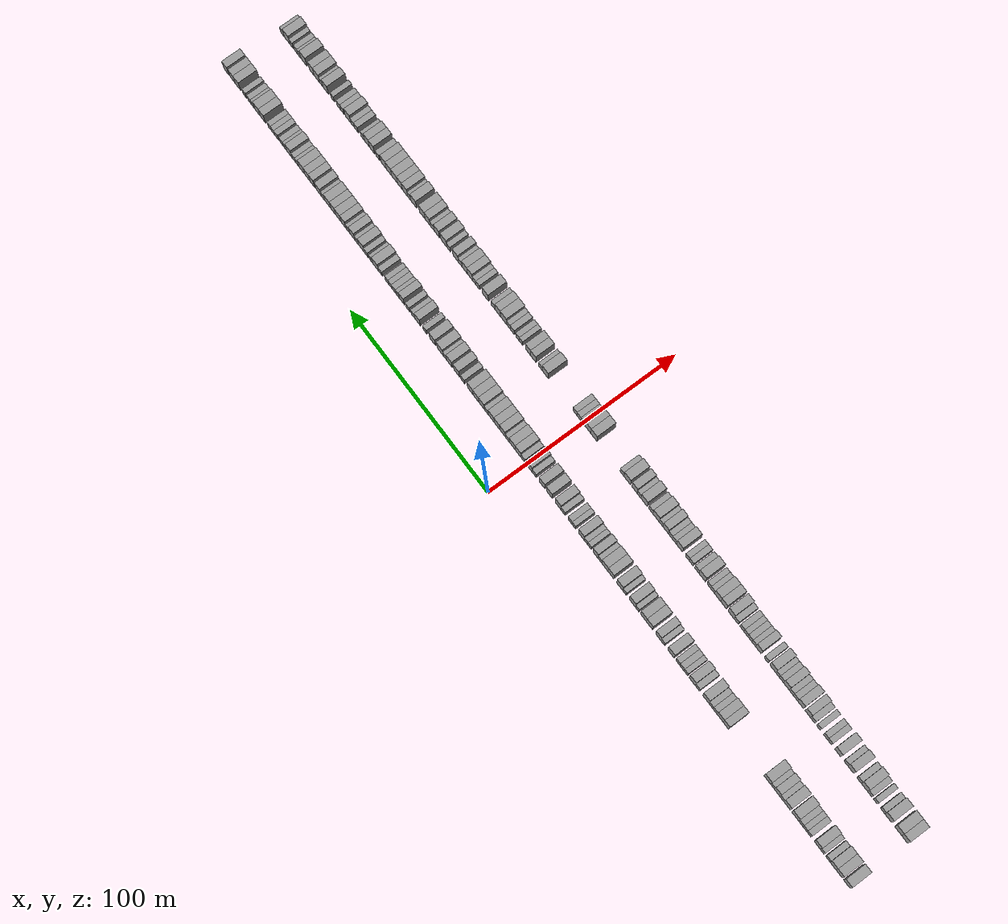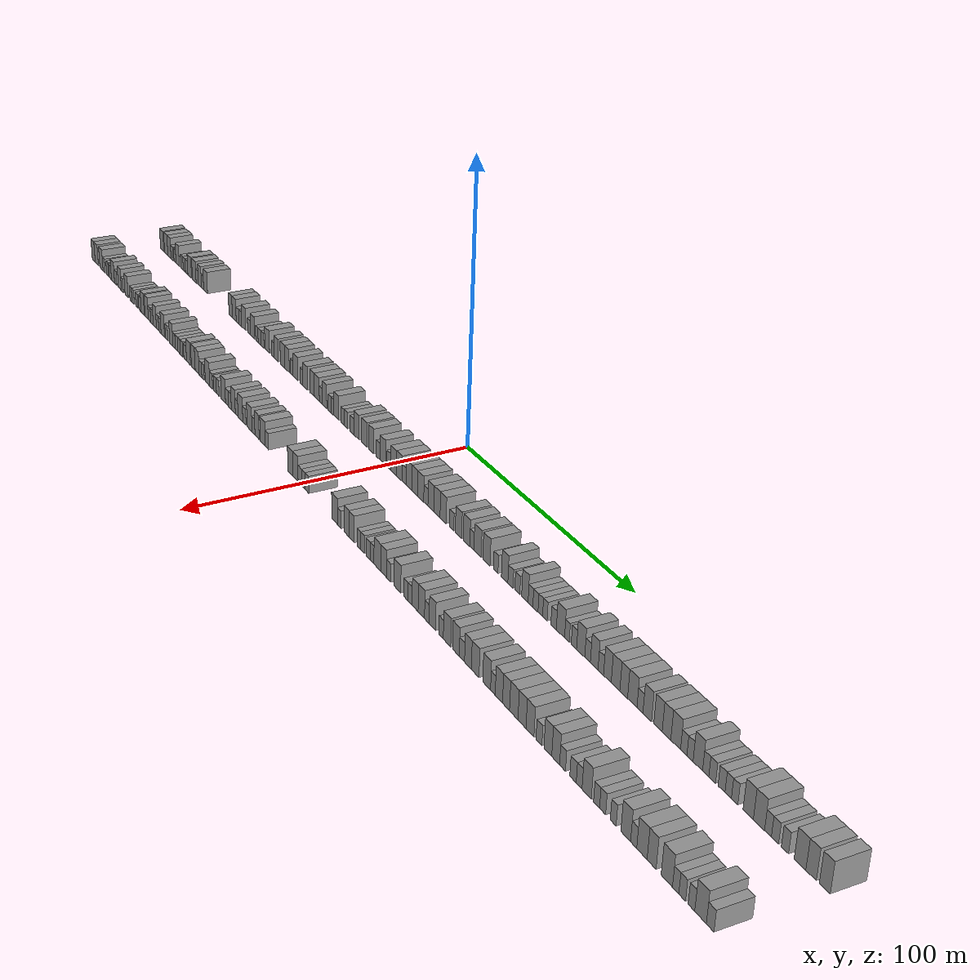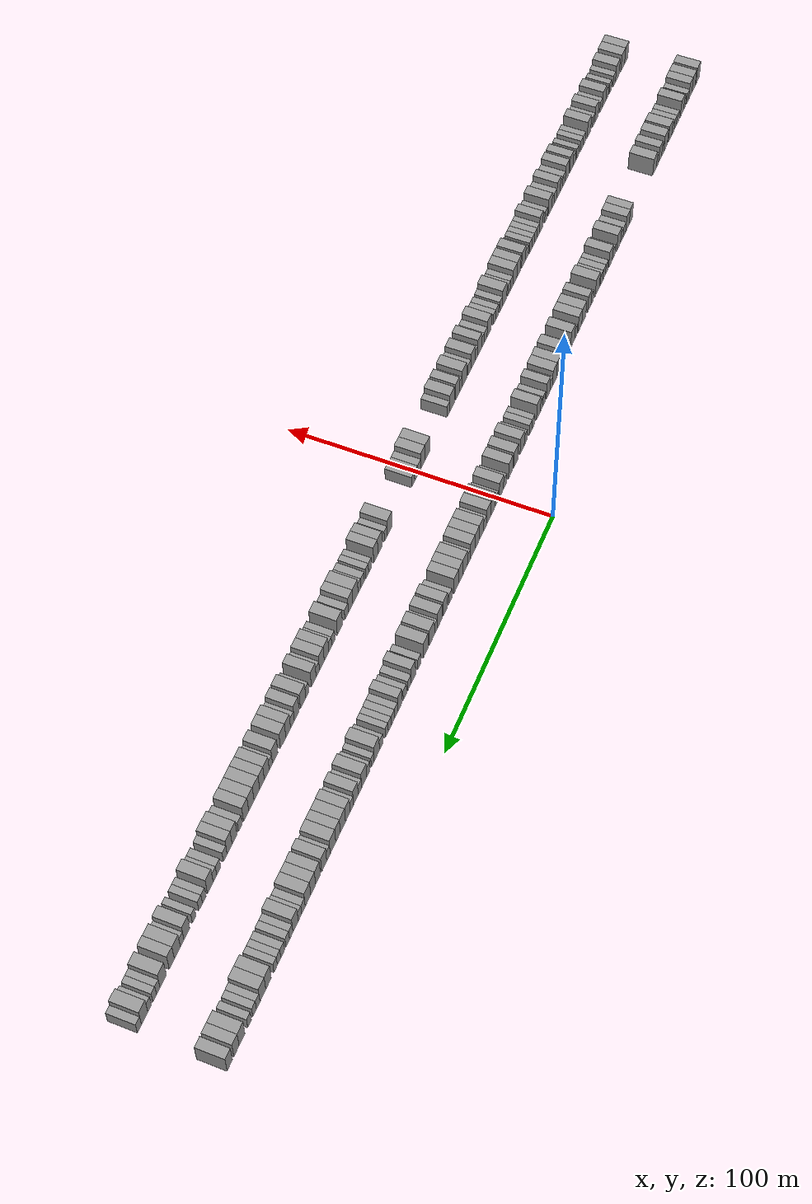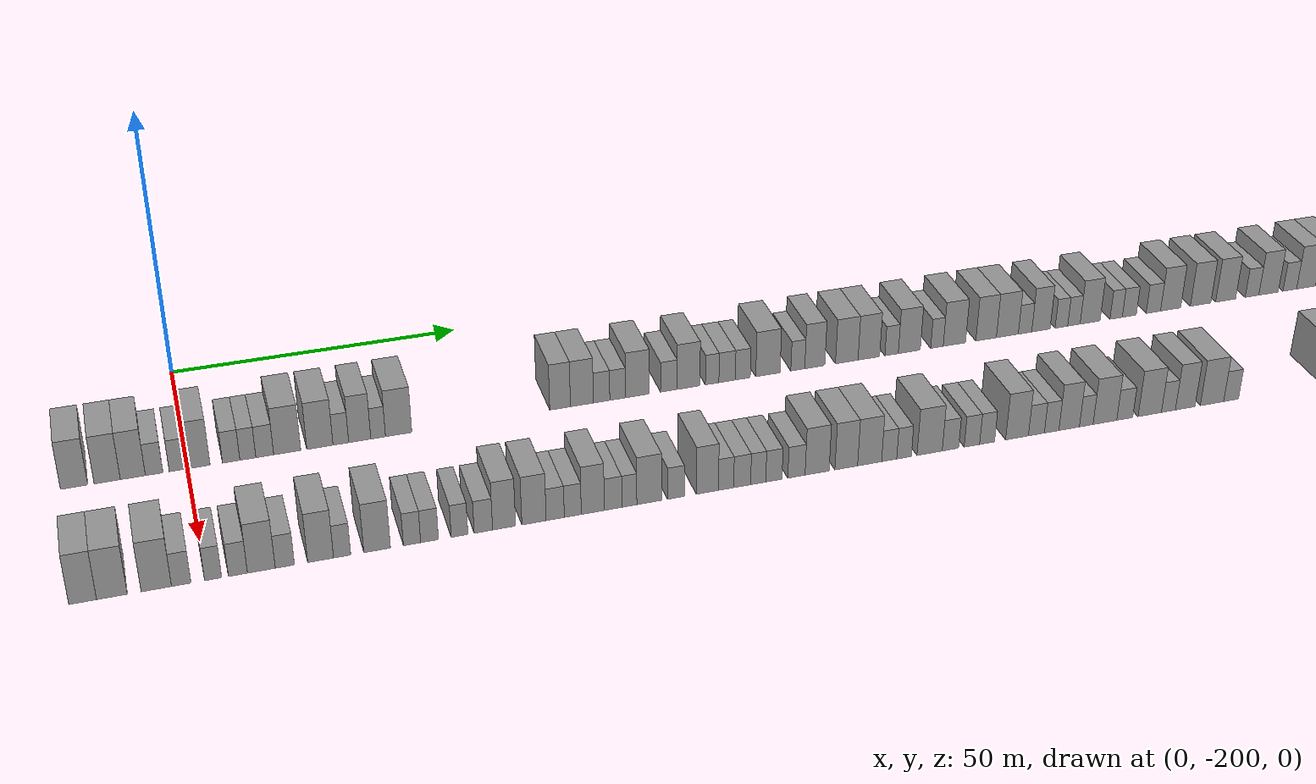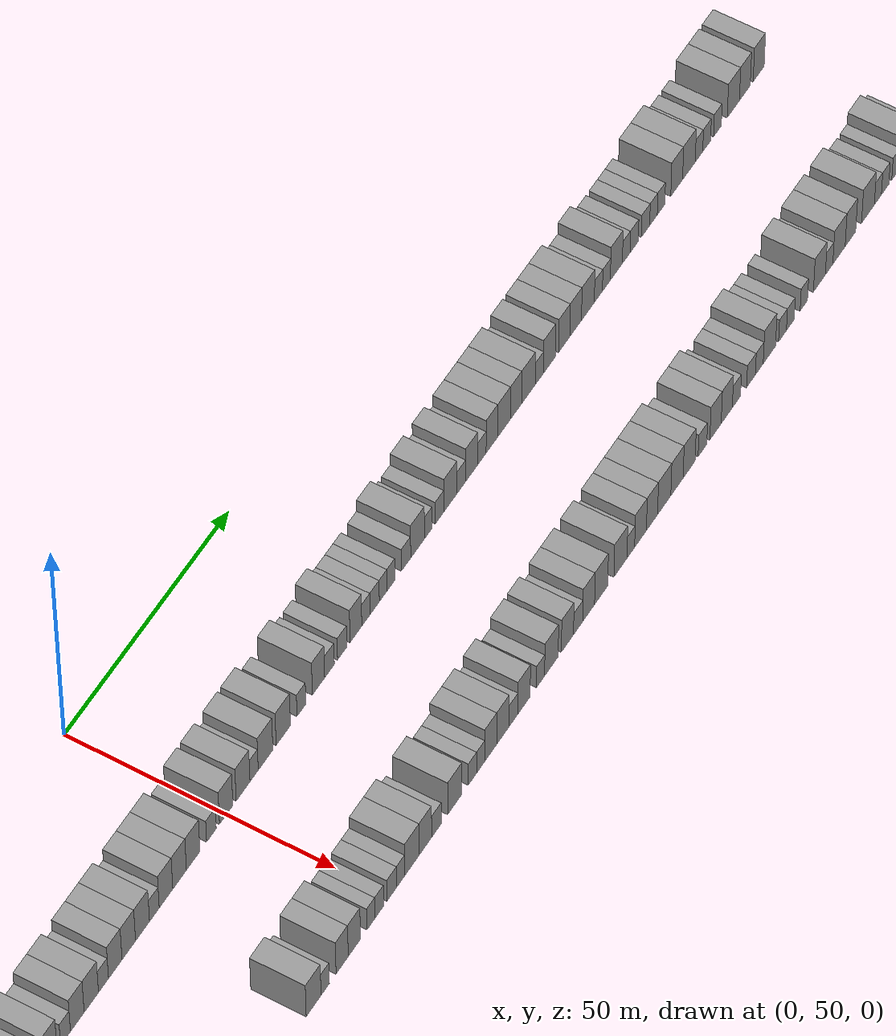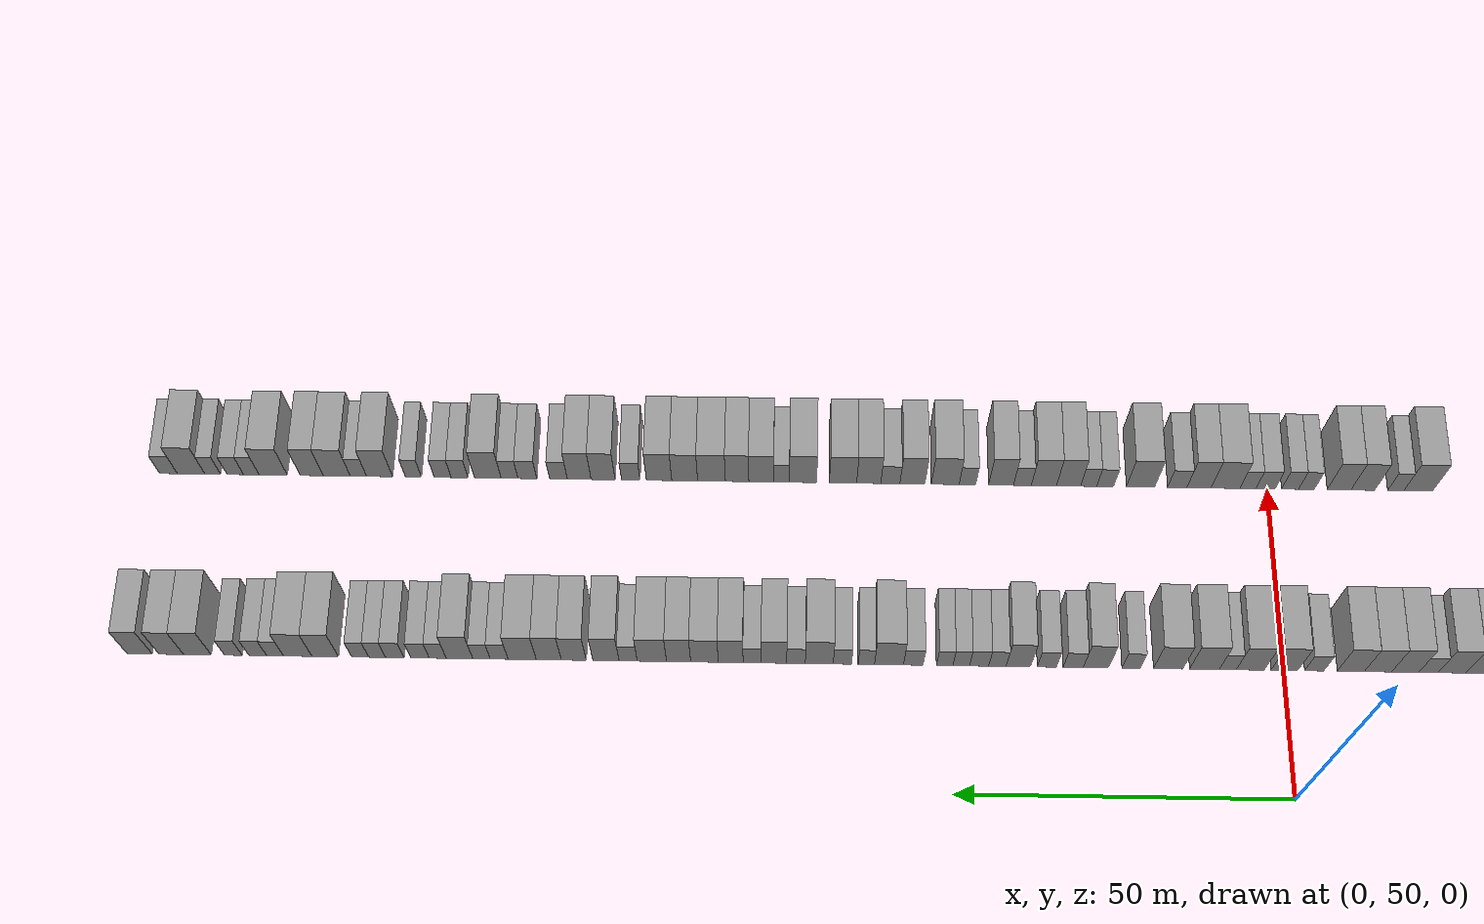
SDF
<sdf version="1.6">
 <world name="default">
  <scene>
   <sky><clouds><speed>12</speed></clouds></sky>
   <ambient>0.4 0.4 0.4 1</ambient>
   <background>0.7 0.7 0.7 1</background>
   <shadows>1</shadows>
  </scene>
  <gravity>0 0 -9.8066</gravity>
  <magnetic_field>6e-06 2.3e-05 -4.2e-05</magnetic_field>
  <physics default="0" name="default_physics" type="ode">
   <ode>
    <solver>
     <type>quick</type>
     <iters>10</iters>
     <sor>1.0</sor>
     <use_dynamic_moi_rescaling>0</use_dynamic_moi_rescaling>
    </solver>
    <constraints>
     <cfm>0</cfm>
     <erp>0.2</erp>
     <contact_max_correcting_vel>100</contact_max_correcting_vel>
     <contact_surface_layer>0.001</contact_surface_layer>
    </constraints>
   </ode>
   <max_step_size>0.004</max_step_size>
   <real_time_factor>1</real_time_factor>
   <real_time_update_rate>250</real_time_update_rate>
  </physics>
  <light name="sun" type="directional">
   <pose>0 0 10 0 0 0</pose>
   <diffuse>0.8 0.8 0.8 1</diffuse>
   <specular>0.2 0.2 0.2 1</specular>
   <attenuation>
    <range>1000</range>
    <constant>0.9</constant>
    <linear>0.01</linear>
    <quadratic>0.001</quadratic>
   </attenuation>
   <direction>-0.5 0.1 -0.9</direction>
  </light>
  <model name="building_1">
   <static>1</static>
   <pose>25.0000 -217.8854 0 0.000000 0.000000 0.000000</pose>
   <link name="link">
    <pose>0 0 4.50 0 0 0</pose>
    <collision name="collision"><geometry><box><size>10.0000 4.2292 9.0000</size></box></geometry></collision>
    <visual name="visual">
     <cast_shadows>0</cast_shadows>
     <geometry><box><size>10.0000 4.2292 9.0000</size></box></geometry>
     <material>
      <script>
       <uri>model://grey_wall/materials/scripts</uri>
       <uri>model://grey_wall/materials/textures</uri>
       <name>vrc/grey_wall</name>
      </script>
     </material>
    </visual>
   </link>
  </model>
  <model name="building_2">
   <static>1</static>
   <pose>25.0000 -212.7243 0 0.000000 0.000000 0.000000</pose>
   <link name="link">
    <pose>0 0 4.50 0 0 0</pose>
    <collision name="collision"><geometry><box><size>10.0000 4.0931 9.0000</size></box></geometry></collision>
    <visual name="visual">
     <cast_shadows>0</cast_shadows>
     <geometry><box><size>10.0000 4.0931 9.0000</size></box></geometry>
     <material>
      <script>
       <uri>model://grey_wall/materials/scripts</uri>
       <uri>model://grey_wall/materials/textures</uri>
       <name>vrc/grey_wall</name>
      </script>
     </material>
    </visual>
   </link>
  </model>
  <model name="building_3">
   <static>1</static>
   <pose>25.0000 -208.7025 0 0.000000 0.000000 0.000000</pose>
   <link name="link">
    <pose>0 0 4.50 0 0 0</pose>
    <collision name="collision"><geometry><box><size>10.0000 3.9504 9.0000</size></box></geometry></collision>
    <visual name="visual">
     <cast_shadows>0</cast_shadows>
     <geometry><box><size>10.0000 3.9504 9.0000</size></box></geometry>
     <material>
      <script>
       <uri>model://grey_wall/materials/scripts</uri>
       <uri>model://grey_wall/materials/textures</uri>
       <name>vrc/grey_wall</name>
      </script>
     </material>
    </visual>
   </link>
  </model>
  <model name="building_4">
   <static>1</static>
   <pose>25.0000 -205.3398 0 0.000000 0.000000 0.000000</pose>
   <link name="link">
    <pose>0 0 3.00 0 0 0</pose>
    <collision name="collision"><geometry><box><size>10.0000 2.7752 6.0000</size></box></geometry></collision>
    <visual name="visual">
     <cast_shadows>0</cast_shadows>
     <geometry><box><size>10.0000 2.7752 6.0000</size></box></geometry>
     <material>
      <script>
       <uri>model://grey_wall/materials/scripts</uri>
       <uri>model://grey_wall/materials/textures</uri>
       <name>vrc/grey_wall</name>
      </script>
     </material>
    </visual>
   </link>
  </model>
  <model name="building_5">
   <static>1</static>
   <pose>25.0000 -201.7482 0 0.000000 0.000000 0.000000</pose>
   <link name="link">
    <pose>0 0 3.00 0 0 0</pose>
    <collision name="collision"><geometry><box><size>10.0000 2.4080 6.0000</size></box></geometry></collision>
    <visual name="visual">
     <cast_shadows>0</cast_shadows>
     <geometry><box><size>10.0000 2.4080 6.0000</size></box></geometry>
     <material>
      <script>
       <uri>model://grey_wall/materials/scripts</uri>
       <uri>model://grey_wall/materials/textures</uri>
       <name>vrc/grey_wall</name>
      </script>
     </material>
    </visual>
   </link>
  </model>
  <model name="building_6">
   <static>1</static>
   <pose>25.0000 -198.4909 0 0.000000 0.000000 0.000000</pose>
   <link name="link">
    <pose>0 0 4.50 0 0 0</pose>
    <collision name="collision"><geometry><box><size>10.0000 4.1066 9.0000</size></box></geometry></collision>
    <visual name="visual">
     <cast_shadows>0</cast_shadows>
     <geometry><box><size>10.0000 4.1066 9.0000</size></box></geometry>
     <material>
      <script>
       <uri>model://grey_wall/materials/scripts</uri>
       <uri>model://grey_wall/materials/textures</uri>
       <name>vrc/grey_wall</name>
      </script>
     </material>
    </visual>
   </link>
  </model>
  <model name="building_7">
   <static>1</static>
   <pose>25.0000 -193.0438 0 0.000000 0.000000 0.000000</pose>
   <link name="link">
    <pose>0 0 3.00 0 0 0</pose>
    <collision name="collision"><geometry><box><size>10.0000 2.7875 6.0000</size></box></geometry></collision>
    <visual name="visual">
     <cast_shadows>0</cast_shadows>
     <geometry><box><size>10.0000 2.7875 6.0000</size></box></geometry>
     <material>
      <script>
       <uri>model://grey_wall/materials/scripts</uri>
       <uri>model://grey_wall/materials/textures</uri>
       <name>vrc/grey_wall</name>
      </script>
     </material>
    </visual>
   </link>
  </model>
  <model name="building_8">
   <static>1</static>
   <pose>25.0000 -190.3522 0 0.000000 0.000000 0.000000</pose>
   <link name="link">
    <pose>0 0 3.00 0 0 0</pose>
    <collision name="collision"><geometry><box><size>10.0000 2.5958 6.0000</size></box></geometry></collision>
    <visual name="visual">
     <cast_shadows>0</cast_shadows>
     <geometry><box><size>10.0000 2.5958 6.0000</size></box></geometry>
     <material>
      <script>
       <uri>model://grey_wall/materials/scripts</uri>
       <uri>model://grey_wall/materials/textures</uri>
       <name>vrc/grey_wall</name>
      </script>
     </material>
    </visual>
   </link>
  </model>
  <model name="building_9">
   <static>1</static>
   <pose>25.0000 -187.6102 0 0.000000 0.000000 0.000000</pose>
   <link name="link">
    <pose>0 0 3.00 0 0 0</pose>
    <collision name="collision"><geometry><box><size>10.0000 2.8883 6.0000</size></box></geometry></collision>
    <visual name="visual">
     <cast_shadows>0</cast_shadows>
     <geometry><box><size>10.0000 2.8883 6.0000</size></box></geometry>
     <material>
      <script>
       <uri>model://grey_wall/materials/scripts</uri>
       <uri>model://grey_wall/materials/textures</uri>
       <name>vrc/grey_wall</name>
      </script>
     </material>
    </visual>
   </link>
  </model>
  <model name="building_10">
   <static>1</static>
   <pose>25.0000 -183.9573 0 0.000000 0.000000 0.000000</pose>
   <link name="link">
    <pose>0 0 4.50 0 0 0</pose>
    <collision name="collision"><geometry><box><size>10.0000 4.4174 9.0000</size></box></geometry></collision>
    <visual name="visual">
     <cast_shadows>0</cast_shadows>
     <geometry><box><size>10.0000 4.4174 9.0000</size></box></geometry>
     <material>
      <script>
       <uri>model://grey_wall/materials/scripts</uri>
       <uri>model://grey_wall/materials/textures</uri>
       <name>vrc/grey_wall</name>
      </script>
     </material>
    </visual>
   </link>
  </model>
  <model name="building_11">
   <static>1</static>
   <pose>25.0000 -178.5948 0 0.000000 0.000000 0.000000</pose>
   <link name="link">
    <pose>0 0 4.50 0 0 0</pose>
    <collision name="collision"><geometry><box><size>10.0000 4.3075 9.0000</size></box></geometry></collision>
    <visual name="visual">
     <cast_shadows>0</cast_shadows>
     <geometry><box><size>10.0000 4.3075 9.0000</size></box></geometry>
     <material>
      <script>
       <uri>model://grey_wall/materials/scripts</uri>
       <uri>model://grey_wall/materials/textures</uri>
       <name>vrc/grey_wall</name>
      </script>
     </material>
    </visual>
   </link>
  </model>
  <model name="building_12">
   <static>1</static>
   <pose>25.0000 -175.1454 0 0.000000 0.000000 0.000000</pose>
   <link name="link">
    <pose>0 0 3.00 0 0 0</pose>
    <collision name="collision"><geometry><box><size>10.0000 2.5914 6.0000</size></box></geometry></collision>
    <visual name="visual">
     <cast_shadows>0</cast_shadows>
     <geometry><box><size>10.0000 2.5914 6.0000</size></box></geometry>
     <material>
      <script>
       <uri>model://grey_wall/materials/scripts</uri>
       <uri>model://grey_wall/materials/textures</uri>
       <name>vrc/grey_wall</name>
      </script>
     </material>
    </visual>
   </link>
  </model>
  <model name="building_13">
   <static>1</static>
   <pose>25.0000 -172.0141 0 0.000000 0.000000 0.000000</pose>
   <link name="link">
    <pose>0 0 4.50 0 0 0</pose>
    <collision name="collision"><geometry><box><size>10.0000 3.6710 9.0000</size></box></geometry></collision>
    <visual name="visual">
     <cast_shadows>0</cast_shadows>
     <geometry><box><size>10.0000 3.6710 9.0000</size></box></geometry>
     <material>
      <script>
       <uri>model://grey_wall/materials/scripts</uri>
       <uri>model://grey_wall/materials/textures</uri>
       <name>vrc/grey_wall</name>
      </script>
     </material>
    </visual>
   </link>
  </model>
  <model name="building_14">
   <static>1</static>
   <pose>25.0000 -168.9576 0 0.000000 0.000000 0.000000</pose>
   <link name="link">
    <pose>0 0 3.00 0 0 0</pose>
    <collision name="collision"><geometry><box><size>10.0000 2.4421 6.0000</size></box></geometry></collision>
    <visual name="visual">
     <cast_shadows>0</cast_shadows>
     <geometry><box><size>10.0000 2.4421 6.0000</size></box></geometry>
     <material>
      <script>
       <uri>model://grey_wall/materials/scripts</uri>
       <uri>model://grey_wall/materials/textures</uri>
       <name>vrc/grey_wall</name>
      </script>
     </material>
    </visual>
   </link>
  </model>
  <model name="building_15">
   <static>1</static>
   <pose>25.0000 -165.5291 0 0.000000 0.000000 0.000000</pose>
   <link name="link">
    <pose>0 0 4.50 0 0 0</pose>
    <collision name="collision"><geometry><box><size>10.0000 4.4150 9.0000</size></box></geometry></collision>
    <visual name="visual">
     <cast_shadows>0</cast_shadows>
     <geometry><box><size>10.0000 4.4150 9.0000</size></box></geometry>
     <material>
      <script>
       <uri>model://grey_wall/materials/scripts</uri>
       <uri>model://grey_wall/materials/textures</uri>
       <name>vrc/grey_wall</name>
      </script>
     </material>
    </visual>
   </link>
  </model>
  <model name="building_16">
   <static>1</static>
   <pose>25.0000 -137.9047 0 0.000000 0.000000 0.000000</pose>
   <link name="link">
    <pose>0 0 4.50 0 0 0</pose>
    <collision name="collision"><geometry><box><size>10.0000 3.6113 9.0000</size></box></geometry></collision>
    <visual name="visual">
     <cast_shadows>0</cast_shadows>
     <geometry><box><size>10.0000 3.6113 9.0000</size></box></geometry>
     <material>
      <script>
       <uri>model://grey_wall/materials/scripts</uri>
       <uri>model://grey_wall/materials/textures</uri>
       <name>vrc/grey_wall</name>
      </script>
     </material>
    </visual>
   </link>
  </model>
  <model name="building_17">
   <static>1</static>
   <pose>25.0000 -134.0874 0 0.000000 0.000000 0.000000</pose>
   <link name="link">
    <pose>0 0 4.50 0 0 0</pose>
    <collision name="collision"><geometry><box><size>10.0000 4.0233 9.0000</size></box></geometry></collision>
    <visual name="visual">
     <cast_shadows>0</cast_shadows>
     <geometry><box><size>10.0000 4.0233 9.0000</size></box></geometry>
     <material>
      <script>
       <uri>model://grey_wall/materials/scripts</uri>
       <uri>model://grey_wall/materials/textures</uri>
       <name>vrc/grey_wall</name>
      </script>
     </material>
    </visual>
   </link>
  </model>
  <model name="building_18">
   <static>1</static>
   <pose>25.0000 -130.6236 0 0.000000 0.000000 0.000000</pose>
   <link name="link">
    <pose>0 0 3.00 0 0 0</pose>
    <collision name="collision"><geometry><box><size>10.0000 2.9042 6.0000</size></box></geometry></collision>
    <visual name="visual">
     <cast_shadows>0</cast_shadows>
     <geometry><box><size>10.0000 2.9042 6.0000</size></box></geometry>
     <material>
      <script>
       <uri>model://grey_wall/materials/scripts</uri>
       <uri>model://grey_wall/materials/textures</uri>
       <name>vrc/grey_wall</name>
      </script>
     </material>
    </visual>
   </link>
  </model>
  <model name="building_19">
   <static>1</static>
   <pose>25.0000 -127.7901 0 0.000000 0.000000 0.000000</pose>
   <link name="link">
    <pose>0 0 3.00 0 0 0</pose>
    <collision name="collision"><geometry><box><size>10.0000 2.7628 6.0000</size></box></geometry></collision>
    <visual name="visual">
     <cast_shadows>0</cast_shadows>
     <geometry><box><size>10.0000 2.7628 6.0000</size></box></geometry>
     <material>
      <script>
       <uri>model://grey_wall/materials/scripts</uri>
       <uri>model://grey_wall/materials/textures</uri>
       <name>vrc/grey_wall</name>
      </script>
     </material>
    </visual>
   </link>
  </model>
  <model name="building_20">
   <static>1</static>
   <pose>25.0000 -124.2791 0 0.000000 0.000000 0.000000</pose>
   <link name="link">
    <pose>0 0 4.50 0 0 0</pose>
    <collision name="collision"><geometry><box><size>10.0000 4.2591 9.0000</size></box></geometry></collision>
    <visual name="visual">
     <cast_shadows>0</cast_shadows>
     <geometry><box><size>10.0000 4.2591 9.0000</size></box></geometry>
     <material>
      <script>
       <uri>model://grey_wall/materials/scripts</uri>
       <uri>model://grey_wall/materials/textures</uri>
       <name>vrc/grey_wall</name>
      </script>
     </material>
    </visual>
   </link>
  </model>
  <model name="building_21">
   <static>1</static>
   <pose>25.0000 -118.6616 0 0.000000 0.000000 0.000000</pose>
   <link name="link">
    <pose>0 0 3.00 0 0 0</pose>
    <collision name="collision"><geometry><box><size>10.0000 2.9758 6.0000</size></box></geometry></collision>
    <visual name="visual">
     <cast_shadows>0</cast_shadows>
     <geometry><box><size>10.0000 2.9758 6.0000</size></box></geometry>
     <material>
      <script>
       <uri>model://grey_wall/materials/scripts</uri>
       <uri>model://grey_wall/materials/textures</uri>
       <name>vrc/grey_wall</name>
      </script>
     </material>
    </visual>
   </link>
  </model>
  <model name="building_22">
   <static>1</static>
   <pose>25.0000 -115.1251 0 0.000000 0.000000 0.000000</pose>
   <link name="link">
    <pose>0 0 4.50 0 0 0</pose>
    <collision name="collision"><geometry><box><size>10.0000 4.0973 9.0000</size></box></geometry></collision>
    <visual name="visual">
     <cast_shadows>0</cast_shadows>
     <geometry><box><size>10.0000 4.0973 9.0000</size></box></geometry>
     <material>
      <script>
       <uri>model://grey_wall/materials/scripts</uri>
       <uri>model://grey_wall/materials/textures</uri>
       <name>vrc/grey_wall</name>
      </script>
     </material>
    </visual>
   </link>
  </model>
  <model name="building_23">
   <static>1</static>
   <pose>25.0000 -110.8517 0 0.000000 0.000000 0.000000</pose>
   <link name="link">
    <pose>0 0 3.00 0 0 0</pose>
    <collision name="collision"><geometry><box><size>10.0000 2.4496 6.0000</size></box></geometry></collision>
    <visual name="visual">
     <cast_shadows>0</cast_shadows>
     <geometry><box><size>10.0000 2.4496 6.0000</size></box></geometry>
     <material>
      <script>
       <uri>model://grey_wall/materials/scripts</uri>
       <uri>model://grey_wall/materials/textures</uri>
       <name>vrc/grey_wall</name>
      </script>
     </material>
    </visual>
   </link>
  </model>
  <model name="building_24">
   <static>1</static>
   <pose>25.0000 -108.1369 0 0.000000 0.000000 0.000000</pose>
   <link name="link">
    <pose>0 0 3.00 0 0 0</pose>
    <collision name="collision"><geometry><box><size>10.0000 2.9800 6.0000</size></box></geometry></collision>
    <visual name="visual">
     <cast_shadows>0</cast_shadows>
     <geometry><box><size>10.0000 2.9800 6.0000</size></box></geometry>
     <material>
      <script>
       <uri>model://grey_wall/materials/scripts</uri>
       <uri>model://grey_wall/materials/textures</uri>
       <name>vrc/grey_wall</name>
      </script>
     </material>
    </visual>
   </link>
  </model>
  <model name="building_25">
   <static>1</static>
   <pose>25.0000 -105.2739 0 0.000000 0.000000 0.000000</pose>
   <link name="link">
    <pose>0 0 3.00 0 0 0</pose>
    <collision name="collision"><geometry><box><size>10.0000 2.7460 6.0000</size></box></geometry></collision>
    <visual name="visual">
     <cast_shadows>0</cast_shadows>
     <geometry><box><size>10.0000 2.7460 6.0000</size></box></geometry>
     <material>
      <script>
       <uri>model://grey_wall/materials/scripts</uri>
       <uri>model://grey_wall/materials/textures</uri>
       <name>vrc/grey_wall</name>
      </script>
     </material>
    </visual>
   </link>
  </model>
  <model name="building_26">
   <static>1</static>
   <pose>25.0000 -100.6678 0 0.000000 0.000000 0.000000</pose>
   <link name="link">
    <pose>0 0 4.50 0 0 0</pose>
    <collision name="collision"><geometry><box><size>10.0000 4.4663 9.0000</size></box></geometry></collision>
    <visual name="visual">
     <cast_shadows>0</cast_shadows>
     <geometry><box><size>10.0000 4.4663 9.0000</size></box></geometry>
     <material>
      <script>
       <uri>model://grey_wall/materials/scripts</uri>
       <uri>model://grey_wall/materials/textures</uri>
       <name>vrc/grey_wall</name>
      </script>
     </material>
    </visual>
   </link>
  </model>
  <model name="building_27">
   <static>1</static>
   <pose>25.0000 -95.1446 0 0.000000 0.000000 0.000000</pose>
   <link name="link">
    <pose>0 0 3.00 0 0 0</pose>
    <collision name="collision"><geometry><box><size>10.0000 2.5802 6.0000</size></box></geometry></collision>
    <visual name="visual">
     <cast_shadows>0</cast_shadows>
     <geometry><box><size>10.0000 2.5802 6.0000</size></box></geometry>
     <material>
      <script>
       <uri>model://grey_wall/materials/scripts</uri>
       <uri>model://grey_wall/materials/textures</uri>
       <name>vrc/grey_wall</name>
      </script>
     </material>
    </visual>
   </link>
  </model>
  <model name="building_28">
   <static>1</static>
   <pose>25.0000 -91.9879 0 0.000000 0.000000 0.000000</pose>
   <link name="link">
    <pose>0 0 4.50 0 0 0</pose>
    <collision name="collision"><geometry><box><size>10.0000 3.7331 9.0000</size></box></geometry></collision>
    <visual name="visual">
     <cast_shadows>0</cast_shadows>
     <geometry><box><size>10.0000 3.7331 9.0000</size></box></geometry>
     <material>
      <script>
       <uri>model://grey_wall/materials/scripts</uri>
       <uri>model://grey_wall/materials/textures</uri>
       <name>vrc/grey_wall</name>
      </script>
     </material>
    </visual>
   </link>
  </model>
  <model name="building_29">
   <static>1</static>
   <pose>25.0000 -86.0032 0 0.000000 0.000000 0.000000</pose>
   <link name="link">
    <pose>0 0 4.50 0 0 0</pose>
    <collision name="collision"><geometry><box><size>10.0000 4.2364 9.0000</size></box></geometry></collision>
    <visual name="visual">
     <cast_shadows>0</cast_shadows>
     <geometry><box><size>10.0000 4.2364 9.0000</size></box></geometry>
     <material>
      <script>
       <uri>model://grey_wall/materials/scripts</uri>
       <uri>model://grey_wall/materials/textures</uri>
       <name>vrc/grey_wall</name>
      </script>
     </material>
    </visual>
   </link>
  </model>
  <model name="building_30">
   <static>1</static>
   <pose>25.0000 -81.8449 0 0.000000 0.000000 0.000000</pose>
   <link name="link">
    <pose>0 0 4.50 0 0 0</pose>
    <collision name="collision"><geometry><box><size>10.0000 4.0802 9.0000</size></box></geometry></collision>
    <visual name="visual">
     <cast_shadows>0</cast_shadows>
     <geometry><box><size>10.0000 4.0802 9.0000</size></box></geometry>
     <material>
      <script>
       <uri>model://grey_wall/materials/scripts</uri>
       <uri>model://grey_wall/materials/textures</uri>
       <name>vrc/grey_wall</name>
      </script>
     </material>
    </visual>
   </link>
  </model>
  <model name="building_31">
   <static>1</static>
   <pose>25.0000 -77.5359 0 0.000000 0.000000 0.000000</pose>
   <link name="link">
    <pose>0 0 3.00 0 0 0</pose>
    <collision name="collision"><geometry><box><size>10.0000 2.5377 6.0000</size></box></geometry></collision>
    <visual name="visual">
     <cast_shadows>0</cast_shadows>
     <geometry><box><size>10.0000 2.5377 6.0000</size></box></geometry>
     <material>
      <script>
       <uri>model://grey_wall/materials/scripts</uri>
       <uri>model://grey_wall/materials/textures</uri>
       <name>vrc/grey_wall</name>
      </script>
     </material>
    </visual>
   </link>
  </model>
  <model name="building_32">
   <static>1</static>
   <pose>25.0000 -74.1695 0 0.000000 0.000000 0.000000</pose>
   <link name="link">
    <pose>0 0 4.50 0 0 0</pose>
    <collision name="collision"><geometry><box><size>10.0000 4.1952 9.0000</size></box></geometry></collision>
    <visual name="visual">
     <cast_shadows>0</cast_shadows>
     <geometry><box><size>10.0000 4.1952 9.0000</size></box></geometry>
     <material>
      <script>
       <uri>model://grey_wall/materials/scripts</uri>
       <uri>model://grey_wall/materials/textures</uri>
       <name>vrc/grey_wall</name>
      </script>
     </material>
    </visual>
   </link>
  </model>
  <model name="building_33">
   <static>1</static>
   <pose>25.0000 -68.8646 0 0.000000 0.000000 0.000000</pose>
   <link name="link">
    <pose>0 0 3.00 0 0 0</pose>
    <collision name="collision"><geometry><box><size>10.0000 2.4146 6.0000</size></box></geometry></collision>
    <visual name="visual">
     <cast_shadows>0</cast_shadows>
     <geometry><box><size>10.0000 2.4146 6.0000</size></box></geometry>
     <material>
      <script>
       <uri>model://grey_wall/materials/scripts</uri>
       <uri>model://grey_wall/materials/textures</uri>
       <name>vrc/grey_wall</name>
      </script>
     </material>
    </visual>
   </link>
  </model>
  <model name="building_34">
   <static>1</static>
   <pose>25.0000 -65.5023 0 0.000000 0.000000 0.000000</pose>
   <link name="link">
    <pose>0 0 4.50 0 0 0</pose>
    <collision name="collision"><geometry><box><size>10.0000 4.3100 9.0000</size></box></geometry></collision>
    <visual name="visual">
     <cast_shadows>0</cast_shadows>
     <geometry><box><size>10.0000 4.3100 9.0000</size></box></geometry>
     <material>
      <script>
       <uri>model://grey_wall/materials/scripts</uri>
       <uri>model://grey_wall/materials/textures</uri>
       <name>vrc/grey_wall</name>
      </script>
     </material>
    </visual>
   </link>
  </model>
  <model name="building_35">
   <static>1</static>
   <pose>25.0000 -59.3474 0 0.000000 0.000000 0.000000</pose>
   <link name="link">
    <pose>0 0 4.50 0 0 0</pose>
    <collision name="collision"><geometry><box><size>10.0000 3.9999 9.0000</size></box></geometry></collision>
    <visual name="visual">
     <cast_shadows>0</cast_shadows>
     <geometry><box><size>10.0000 3.9999 9.0000</size></box></geometry>
     <material>
      <script>
       <uri>model://grey_wall/materials/scripts</uri>
       <uri>model://grey_wall/materials/textures</uri>
       <name>vrc/grey_wall</name>
      </script>
     </material>
    </visual>
   </link>
  </model>
  <model name="building_36">
   <static>1</static>
   <pose>25.0000 -55.2060 0 0.000000 0.000000 0.000000</pose>
   <link name="link">
    <pose>0 0 4.50 0 0 0</pose>
    <collision name="collision"><geometry><box><size>10.0000 4.2829 9.0000</size></box></geometry></collision>
    <visual name="visual">
     <cast_shadows>0</cast_shadows>
     <geometry><box><size>10.0000 4.2829 9.0000</size></box></geometry>
     <material>
      <script>
       <uri>model://grey_wall/materials/scripts</uri>
       <uri>model://grey_wall/materials/textures</uri>
       <name>vrc/grey_wall</name>
      </script>
     </material>
    </visual>
   </link>
  </model>
  <model name="building_37">
   <static>1</static>
   <pose>25.0000 -51.7401 0 0.000000 0.000000 0.000000</pose>
   <link name="link">
    <pose>0 0 3.00 0 0 0</pose>
    <collision name="collision"><geometry><box><size>10.0000 2.6489 6.0000</size></box></geometry></collision>
    <visual name="visual">
     <cast_shadows>0</cast_shadows>
     <geometry><box><size>10.0000 2.6489 6.0000</size></box></geometry>
     <material>
      <script>
       <uri>model://grey_wall/materials/scripts</uri>
       <uri>model://grey_wall/materials/textures</uri>
       <name>vrc/grey_wall</name>
      </script>
     </material>
    </visual>
   </link>
  </model>
  <model name="building_38">
   <static>1</static>
   <pose>25.0000 -48.6042 0 0.000000 0.000000 0.000000</pose>
   <link name="link">
    <pose>0 0 4.50 0 0 0</pose>
    <collision name="collision"><geometry><box><size>10.0000 3.6230 9.0000</size></box></geometry></collision>
    <visual name="visual">
     <cast_shadows>0</cast_shadows>
     <geometry><box><size>10.0000 3.6230 9.0000</size></box></geometry>
     <material>
      <script>
       <uri>model://grey_wall/materials/scripts</uri>
       <uri>model://grey_wall/materials/textures</uri>
       <name>vrc/grey_wall</name>
      </script>
     </material>
    </visual>
   </link>
  </model>
  <model name="building_39">
   <static>1</static>
   <pose>25.0000 -44.5443 0 0.000000 0.000000 0.000000</pose>
   <link name="link">
    <pose>0 0 3.00 0 0 0</pose>
    <collision name="collision"><geometry><box><size>10.0000 2.4967 6.0000</size></box></geometry></collision>
    <visual name="visual">
     <cast_shadows>0</cast_shadows>
     <geometry><box><size>10.0000 2.4967 6.0000</size></box></geometry>
     <material>
      <script>
       <uri>model://grey_wall/materials/scripts</uri>
       <uri>model://grey_wall/materials/textures</uri>
       <name>vrc/grey_wall</name>
      </script>
     </material>
    </visual>
   </link>
  </model>
  <model name="building_40">
   <static>1</static>
   <pose>25.0000 -42.0547 0 0.000000 0.000000 0.000000</pose>
   <link name="link">
    <pose>0 0 3.00 0 0 0</pose>
    <collision name="collision"><geometry><box><size>10.0000 2.4824 6.0000</size></box></geometry></collision>
    <visual name="visual">
     <cast_shadows>0</cast_shadows>
     <geometry><box><size>10.0000 2.4824 6.0000</size></box></geometry>
     <material>
      <script>
       <uri>model://grey_wall/materials/scripts</uri>
       <uri>model://grey_wall/materials/textures</uri>
       <name>vrc/grey_wall</name>
      </script>
     </material>
    </visual>
   </link>
  </model>
  <model name="building_41">
   <static>1</static>
   <pose>25.0000 -38.8183 0 0.000000 0.000000 0.000000</pose>
   <link name="link">
    <pose>0 0 4.50 0 0 0</pose>
    <collision name="collision"><geometry><box><size>10.0000 3.9903 9.0000</size></box></geometry></collision>
    <visual name="visual">
     <cast_shadows>0</cast_shadows>
     <geometry><box><size>10.0000 3.9903 9.0000</size></box></geometry>
     <material>
      <script>
       <uri>model://grey_wall/materials/scripts</uri>
       <uri>model://grey_wall/materials/textures</uri>
       <name>vrc/grey_wall</name>
      </script>
     </material>
    </visual>
   </link>
  </model>
  <model name="building_42">
   <static>1</static>
   <pose>25.0000 -33.5864 0 0.000000 0.000000 0.000000</pose>
   <link name="link">
    <pose>0 0 3.00 0 0 0</pose>
    <collision name="collision"><geometry><box><size>10.0000 2.4735 6.0000</size></box></geometry></collision>
    <visual name="visual">
     <cast_shadows>0</cast_shadows>
     <geometry><box><size>10.0000 2.4735 6.0000</size></box></geometry>
     <material>
      <script>
       <uri>model://grey_wall/materials/scripts</uri>
       <uri>model://grey_wall/materials/textures</uri>
       <name>vrc/grey_wall</name>
      </script>
     </material>
    </visual>
   </link>
  </model>
  <model name="building_43">
   <static>1</static>
   <pose>25.0000 -30.9347 0 0.000000 0.000000 0.000000</pose>
   <link name="link">
    <pose>0 0 3.00 0 0 0</pose>
    <collision name="collision"><geometry><box><size>10.0000 2.8299 6.0000</size></box></geometry></collision>
    <visual name="visual">
     <cast_shadows>0</cast_shadows>
     <geometry><box><size>10.0000 2.8299 6.0000</size></box></geometry>
     <material>
      <script>
       <uri>model://grey_wall/materials/scripts</uri>
       <uri>model://grey_wall/materials/textures</uri>
       <name>vrc/grey_wall</name>
      </script>
     </material>
    </visual>
   </link>
  </model>
  <model name="building_44">
   <static>1</static>
   <pose>25.0000 -26.0510 0 0.000000 0.000000 0.000000</pose>
   <link name="link">
    <pose>0 0 3.00 0 0 0</pose>
    <collision name="collision"><geometry><box><size>10.0000 2.9376 6.0000</size></box></geometry></collision>
    <visual name="visual">
     <cast_shadows>0</cast_shadows>
     <geometry><box><size>10.0000 2.9376 6.0000</size></box></geometry>
     <material>
      <script>
       <uri>model://grey_wall/materials/scripts</uri>
       <uri>model://grey_wall/materials/textures</uri>
       <name>vrc/grey_wall</name>
      </script>
     </material>
    </visual>
   </link>
  </model>
  <model name="building_45">
   <static>1</static>
   <pose>25.0000 -22.5255 0 0.000000 0.000000 0.000000</pose>
   <link name="link">
    <pose>0 0 4.50 0 0 0</pose>
    <collision name="collision"><geometry><box><size>10.0000 4.1135 9.0000</size></box></geometry></collision>
    <visual name="visual">
     <cast_shadows>0</cast_shadows>
     <geometry><box><size>10.0000 4.1135 9.0000</size></box></geometry>
     <material>
      <script>
       <uri>model://grey_wall/materials/scripts</uri>
       <uri>model://grey_wall/materials/textures</uri>
       <name>vrc/grey_wall</name>
      </script>
     </material>
    </visual>
   </link>
  </model>
  <model name="building_46">
   <static>1</static>
   <pose>25.0000 -16.3590 0 0.000000 0.000000 0.000000</pose>
   <link name="link">
    <pose>0 0 4.50 0 0 0</pose>
    <collision name="collision"><geometry><box><size>10.0000 4.2193 9.0000</size></box></geometry></collision>
    <visual name="visual">
     <cast_shadows>0</cast_shadows>
     <geometry><box><size>10.0000 4.2193 9.0000</size></box></geometry>
     <material>
      <script>
       <uri>model://grey_wall/materials/scripts</uri>
       <uri>model://grey_wall/materials/textures</uri>
       <name>vrc/grey_wall</name>
      </script>
     </material>
    </visual>
   </link>
  </model>
  <model name="building_47">
   <static>1</static>
   <pose>25.0000 -11.1760 0 0.000000 0.000000 0.000000</pose>
   <link name="link">
    <pose>0 0 4.50 0 0 0</pose>
    <collision name="collision"><geometry><box><size>10.0000 4.1468 9.0000</size></box></geometry></collision>
    <visual name="visual">
     <cast_shadows>0</cast_shadows>
     <geometry><box><size>10.0000 4.1468 9.0000</size></box></geometry>
     <material>
      <script>
       <uri>model://grey_wall/materials/scripts</uri>
       <uri>model://grey_wall/materials/textures</uri>
       <name>vrc/grey_wall</name>
      </script>
     </material>
    </visual>
   </link>
  </model>
  <model name="building_48">
   <static>1</static>
   <pose>25.0000 -5.6765 0 0.000000 0.000000 0.000000</pose>
   <link name="link">
    <pose>0 0 3.00 0 0 0</pose>
    <collision name="collision"><geometry><box><size>10.0000 2.8521 6.0000</size></box></geometry></collision>
    <visual name="visual">
     <cast_shadows>0</cast_shadows>
     <geometry><box><size>10.0000 2.8521 6.0000</size></box></geometry>
     <material>
      <script>
       <uri>model://grey_wall/materials/scripts</uri>
       <uri>model://grey_wall/materials/textures</uri>
       <name>vrc/grey_wall</name>
      </script>
     </material>
    </visual>
   </link>
  </model>
  <model name="building_49">
   <static>1</static>
   <pose>25.0000 -2.2138 0 0.000000 0.000000 0.000000</pose>
   <link name="link">
    <pose>0 0 4.50 0 0 0</pose>
    <collision name="collision"><geometry><box><size>10.0000 4.0734 9.0000</size></box></geometry></collision>
    <visual name="visual">
     <cast_shadows>0</cast_shadows>
     <geometry><box><size>10.0000 4.0734 9.0000</size></box></geometry>
     <material>
      <script>
       <uri>model://grey_wall/materials/scripts</uri>
       <uri>model://grey_wall/materials/textures</uri>
       <name>vrc/grey_wall</name>
      </script>
     </material>
    </visual>
   </link>
  </model>
  <model name="building_50">
   <static>1</static>
   <pose>25.0000 2.2588 0 0.000000 0.000000 0.000000</pose>
   <link name="link">
    <pose>0 0 3.00 0 0 0</pose>
    <collision name="collision"><geometry><box><size>10.0000 2.8717 6.0000</size></box></geometry></collision>
    <visual name="visual">
     <cast_shadows>0</cast_shadows>
     <geometry><box><size>10.0000 2.8717 6.0000</size></box></geometry>
     <material>
      <script>
       <uri>model://grey_wall/materials/scripts</uri>
       <uri>model://grey_wall/materials/textures</uri>
       <name>vrc/grey_wall</name>
      </script>
     </material>
    </visual>
   </link>
  </model>
  <model name="building_51">
   <static>1</static>
   <pose>25.0000 5.7021 0 0.000000 0.000000 0.000000</pose>
   <link name="link">
    <pose>0 0 4.50 0 0 0</pose>
    <collision name="collision"><geometry><box><size>10.0000 4.0148 9.0000</size></box></geometry></collision>
    <visual name="visual">
     <cast_shadows>0</cast_shadows>
     <geometry><box><size>10.0000 4.0148 9.0000</size></box></geometry>
     <material>
      <script>
       <uri>model://grey_wall/materials/scripts</uri>
       <uri>model://grey_wall/materials/textures</uri>
       <name>vrc/grey_wall</name>
      </script>
     </material>
    </visual>
   </link>
  </model>
  <model name="building_52">
   <static>1</static>
   <pose>25.0000 9.8063 0 0.000000 0.000000 0.000000</pose>
   <link name="link">
    <pose>0 0 4.50 0 0 0</pose>
    <collision name="collision"><geometry><box><size>10.0000 4.1936 9.0000</size></box></geometry></collision>
    <visual name="visual">
     <cast_shadows>0</cast_shadows>
     <geometry><box><size>10.0000 4.1936 9.0000</size></box></geometry>
     <material>
      <script>
       <uri>model://grey_wall/materials/scripts</uri>
       <uri>model://grey_wall/materials/textures</uri>
       <name>vrc/grey_wall</name>
      </script>
     </material>
    </visual>
   </link>
  </model>
  <model name="building_53">
   <static>1</static>
   <pose>25.0000 13.3732 0 0.000000 0.000000 0.000000</pose>
   <link name="link">
    <pose>0 0 3.00 0 0 0</pose>
    <collision name="collision"><geometry><box><size>10.0000 2.9401 6.0000</size></box></geometry></collision>
    <visual name="visual">
     <cast_shadows>0</cast_shadows>
     <geometry><box><size>10.0000 2.9401 6.0000</size></box></geometry>
     <material>
      <script>
       <uri>model://grey_wall/materials/scripts</uri>
       <uri>model://grey_wall/materials/textures</uri>
       <name>vrc/grey_wall</name>
      </script>
     </material>
    </visual>
   </link>
  </model>
  <model name="building_54">
   <static>1</static>
   <pose>25.0000 16.8367 0 0.000000 0.000000 0.000000</pose>
   <link name="link">
    <pose>0 0 4.50 0 0 0</pose>
    <collision name="collision"><geometry><box><size>10.0000 3.9869 9.0000</size></box></geometry></collision>
    <visual name="visual">
     <cast_shadows>0</cast_shadows>
     <geometry><box><size>10.0000 3.9869 9.0000</size></box></geometry>
     <material>
      <script>
       <uri>model://grey_wall/materials/scripts</uri>
       <uri>model://grey_wall/materials/textures</uri>
       <name>vrc/grey_wall</name>
      </script>
     </material>
    </visual>
   </link>
  </model>
  <model name="building_55">
   <static>1</static>
   <pose>25.0000 20.8237 0 0.000000 0.000000 0.000000</pose>
   <link name="link">
    <pose>0 0 4.50 0 0 0</pose>
    <collision name="collision"><geometry><box><size>10.0000 3.9871 9.0000</size></box></geometry></collision>
    <visual name="visual">
     <cast_shadows>0</cast_shadows>
     <geometry><box><size>10.0000 3.9871 9.0000</size></box></geometry>
     <material>
      <script>
       <uri>model://grey_wall/materials/scripts</uri>
       <uri>model://grey_wall/materials/textures</uri>
       <name>vrc/grey_wall</name>
      </script>
     </material>
    </visual>
   </link>
  </model>
  <model name="building_56">
   <static>1</static>
   <pose>25.0000 24.8852 0 0.000000 0.000000 0.000000</pose>
   <link name="link">
    <pose>0 0 4.50 0 0 0</pose>
    <collision name="collision"><geometry><box><size>10.0000 4.1360 9.0000</size></box></geometry></collision>
    <visual name="visual">
     <cast_shadows>0</cast_shadows>
     <geometry><box><size>10.0000 4.1360 9.0000</size></box></geometry>
     <material>
      <script>
       <uri>model://grey_wall/materials/scripts</uri>
       <uri>model://grey_wall/materials/textures</uri>
       <name>vrc/grey_wall</name>
      </script>
     </material>
    </visual>
   </link>
  </model>
  <model name="building_57">
   <static>1</static>
   <pose>25.0000 28.3893 0 0.000000 0.000000 0.000000</pose>
   <link name="link">
    <pose>0 0 3.00 0 0 0</pose>
    <collision name="collision"><geometry><box><size>10.0000 2.8722 6.0000</size></box></geometry></collision>
    <visual name="visual">
     <cast_shadows>0</cast_shadows>
     <geometry><box><size>10.0000 2.8722 6.0000</size></box></geometry>
     <material>
      <script>
       <uri>model://grey_wall/materials/scripts</uri>
       <uri>model://grey_wall/materials/textures</uri>
       <name>vrc/grey_wall</name>
      </script>
     </material>
    </visual>
   </link>
  </model>
  <model name="building_58">
   <static>1</static>
   <pose>25.0000 31.8541 0 0.000000 0.000000 0.000000</pose>
   <link name="link">
    <pose>0 0 4.50 0 0 0</pose>
    <collision name="collision"><geometry><box><size>10.0000 4.0575 9.0000</size></box></geometry></collision>
    <visual name="visual">
     <cast_shadows>0</cast_shadows>
     <geometry><box><size>10.0000 4.0575 9.0000</size></box></geometry>
     <material>
      <script>
       <uri>model://grey_wall/materials/scripts</uri>
       <uri>model://grey_wall/materials/textures</uri>
       <name>vrc/grey_wall</name>
      </script>
     </material>
    </visual>
   </link>
  </model>
  <model name="building_59">
   <static>1</static>
   <pose>25.0000 35.9184 0 0.000000 0.000000 0.000000</pose>
   <link name="link">
    <pose>0 0 4.50 0 0 0</pose>
    <collision name="collision"><geometry><box><size>10.0000 4.0711 9.0000</size></box></geometry></collision>
    <visual name="visual">
     <cast_shadows>0</cast_shadows>
     <geometry><box><size>10.0000 4.0711 9.0000</size></box></geometry>
     <material>
      <script>
       <uri>model://grey_wall/materials/scripts</uri>
       <uri>model://grey_wall/materials/textures</uri>
       <name>vrc/grey_wall</name>
      </script>
     </material>
    </visual>
   </link>
  </model>
  <model name="building_60">
   <static>1</static>
   <pose>25.0000 39.9813 0 0.000000 0.000000 0.000000</pose>
   <link name="link">
    <pose>0 0 4.50 0 0 0</pose>
    <collision name="collision"><geometry><box><size>10.0000 4.0546 9.0000</size></box></geometry></collision>
    <visual name="visual">
     <cast_shadows>0</cast_shadows>
     <geometry><box><size>10.0000 4.0546 9.0000</size></box></geometry>
     <material>
      <script>
       <uri>model://grey_wall/materials/scripts</uri>
       <uri>model://grey_wall/materials/textures</uri>
       <name>vrc/grey_wall</name>
      </script>
     </material>
    </visual>
   </link>
  </model>
  <model name="building_61">
   <static>1</static>
   <pose>25.0000 45.4525 0 0.000000 0.000000 0.000000</pose>
   <link name="link">
    <pose>0 0 3.00 0 0 0</pose>
    <collision name="collision"><geometry><box><size>10.0000 2.8880 6.0000</size></box></geometry></collision>
    <visual name="visual">
     <cast_shadows>0</cast_shadows>
     <geometry><box><size>10.0000 2.8880 6.0000</size></box></geometry>
     <material>
      <script>
       <uri>model://grey_wall/materials/scripts</uri>
       <uri>model://grey_wall/materials/textures</uri>
       <name>vrc/grey_wall</name>
      </script>
     </material>
    </visual>
   </link>
  </model>
  <model name="building_62">
   <static>1</static>
   <pose>25.0000 49.9165 0 0.000000 0.000000 0.000000</pose>
   <link name="link">
    <pose>0 0 4.50 0 0 0</pose>
    <collision name="collision"><geometry><box><size>10.0000 4.0400 9.0000</size></box></geometry></collision>
    <visual name="visual">
     <cast_shadows>0</cast_shadows>
     <geometry><box><size>10.0000 4.0400 9.0000</size></box></geometry>
     <material>
      <script>
       <uri>model://grey_wall/materials/scripts</uri>
       <uri>model://grey_wall/materials/textures</uri>
       <name>vrc/grey_wall</name>
      </script>
     </material>
    </visual>
   </link>
  </model>
  <model name="building_63">
   <static>1</static>
   <pose>25.0000 55.0288 0 0.000000 0.000000 0.000000</pose>
   <link name="link">
    <pose>0 0 4.50 0 0 0</pose>
    <collision name="collision"><geometry><box><size>10.0000 4.1845 9.0000</size></box></geometry></collision>
    <visual name="visual">
     <cast_shadows>0</cast_shadows>
     <geometry><box><size>10.0000 4.1845 9.0000</size></box></geometry>
     <material>
      <script>
       <uri>model://grey_wall/materials/scripts</uri>
       <uri>model://grey_wall/materials/textures</uri>
       <name>vrc/grey_wall</name>
      </script>
     </material>
    </visual>
   </link>
  </model>
  <model name="building_64">
   <static>1</static>
   <pose>25.0000 58.3787 0 0.000000 0.000000 0.000000</pose>
   <link name="link">
    <pose>0 0 3.00 0 0 0</pose>
    <collision name="collision"><geometry><box><size>10.0000 2.5154 6.0000</size></box></geometry></collision>
    <visual name="visual">
     <cast_shadows>0</cast_shadows>
     <geometry><box><size>10.0000 2.5154 6.0000</size></box></geometry>
     <material>
      <script>
       <uri>model://grey_wall/materials/scripts</uri>
       <uri>model://grey_wall/materials/textures</uri>
       <name>vrc/grey_wall</name>
      </script>
     </material>
    </visual>
   </link>
  </model>
  <model name="building_65">
   <static>1</static>
   <pose>25.0000 61.8660 0 0.000000 0.000000 0.000000</pose>
   <link name="link">
    <pose>0 0 4.50 0 0 0</pose>
    <collision name="collision"><geometry><box><size>10.0000 4.4591 9.0000</size></box></geometry></collision>
    <visual name="visual">
     <cast_shadows>0</cast_shadows>
     <geometry><box><size>10.0000 4.4591 9.0000</size></box></geometry>
     <material>
      <script>
       <uri>model://grey_wall/materials/scripts</uri>
       <uri>model://grey_wall/materials/textures</uri>
       <name>vrc/grey_wall</name>
      </script>
     </material>
    </visual>
   </link>
  </model>
  <model name="building_66">
   <static>1</static>
   <pose>25.0000 67.2920 0 0.000000 0.000000 0.000000</pose>
   <link name="link">
    <pose>0 0 4.50 0 0 0</pose>
    <collision name="collision"><geometry><box><size>10.0000 4.3930 9.0000</size></box></geometry></collision>
    <visual name="visual">
     <cast_shadows>0</cast_shadows>
     <geometry><box><size>10.0000 4.3930 9.0000</size></box></geometry>
     <material>
      <script>
       <uri>model://grey_wall/materials/scripts</uri>
       <uri>model://grey_wall/materials/textures</uri>
       <name>vrc/grey_wall</name>
      </script>
     </material>
    </visual>
   </link>
  </model>
  <model name="building_67">
   <static>1</static>
   <pose>25.0000 72.8532 0 0.000000 0.000000 0.000000</pose>
   <link name="link">
    <pose>0 0 3.00 0 0 0</pose>
    <collision name="collision"><geometry><box><size>10.0000 2.7295 6.0000</size></box></geometry></collision>
    <visual name="visual">
     <cast_shadows>0</cast_shadows>
     <geometry><box><size>10.0000 2.7295 6.0000</size></box></geometry>
     <material>
      <script>
       <uri>model://grey_wall/materials/scripts</uri>
       <uri>model://grey_wall/materials/textures</uri>
       <name>vrc/grey_wall</name>
      </script>
     </material>
    </visual>
   </link>
  </model>
  <model name="building_68">
   <static>1</static>
   <pose>25.0000 78.1152 0 0.000000 0.000000 0.000000</pose>
   <link name="link">
    <pose>0 0 4.50 0 0 0</pose>
    <collision name="collision"><geometry><box><size>10.0000 3.7944 9.0000</size></box></geometry></collision>
    <visual name="visual">
     <cast_shadows>0</cast_shadows>
     <geometry><box><size>10.0000 3.7944 9.0000</size></box></geometry>
     <material>
      <script>
       <uri>model://grey_wall/materials/scripts</uri>
       <uri>model://grey_wall/materials/textures</uri>
       <name>vrc/grey_wall</name>
      </script>
     </material>
    </visual>
   </link>
  </model>
  <model name="building_69">
   <static>1</static>
   <pose>25.0000 81.5113 0 0.000000 0.000000 0.000000</pose>
   <link name="link">
    <pose>0 0 3.00 0 0 0</pose>
    <collision name="collision"><geometry><box><size>10.0000 2.9978 6.0000</size></box></geometry></collision>
    <visual name="visual">
     <cast_shadows>0</cast_shadows>
     <geometry><box><size>10.0000 2.9978 6.0000</size></box></geometry>
     <material>
      <script>
       <uri>model://grey_wall/materials/scripts</uri>
       <uri>model://grey_wall/materials/textures</uri>
       <name>vrc/grey_wall</name>
      </script>
     </material>
    </visual>
   </link>
  </model>
  <model name="building_70">
   <static>1</static>
   <pose>25.0000 85.4505 0 0.000000 0.000000 0.000000</pose>
   <link name="link">
    <pose>0 0 3.00 0 0 0</pose>
    <collision name="collision"><geometry><box><size>10.0000 2.8807 6.0000</size></box></geometry></collision>
    <visual name="visual">
     <cast_shadows>0</cast_shadows>
     <geometry><box><size>10.0000 2.8807 6.0000</size></box></geometry>
     <material>
      <script>
       <uri>model://grey_wall/materials/scripts</uri>
       <uri>model://grey_wall/materials/textures</uri>
       <name>vrc/grey_wall</name>
      </script>
     </material>
    </visual>
   </link>
  </model>
  <model name="building_71">
   <static>1</static>
   <pose>25.0000 89.7215 0 0.000000 0.000000 0.000000</pose>
   <link name="link">
    <pose>0 0 4.50 0 0 0</pose>
    <collision name="collision"><geometry><box><size>10.0000 3.6614 9.0000</size></box></geometry></collision>
    <visual name="visual">
     <cast_shadows>0</cast_shadows>
     <geometry><box><size>10.0000 3.6614 9.0000</size></box></geometry>
     <material>
      <script>
       <uri>model://grey_wall/materials/scripts</uri>
       <uri>model://grey_wall/materials/textures</uri>
       <name>vrc/grey_wall</name>
      </script>
     </material>
    </visual>
   </link>
  </model>
  <model name="building_72">
   <static>1</static>
   <pose>25.0000 92.8641 0 0.000000 0.000000 0.000000</pose>
   <link name="link">
    <pose>0 0 3.00 0 0 0</pose>
    <collision name="collision"><geometry><box><size>10.0000 2.6238 6.0000</size></box></geometry></collision>
    <visual name="visual">
     <cast_shadows>0</cast_shadows>
     <geometry><box><size>10.0000 2.6238 6.0000</size></box></geometry>
     <material>
      <script>
       <uri>model://grey_wall/materials/scripts</uri>
       <uri>model://grey_wall/materials/textures</uri>
       <name>vrc/grey_wall</name>
      </script>
     </material>
    </visual>
   </link>
  </model>
  <model name="building_73">
   <static>1</static>
   <pose>25.0000 95.6105 0 0.000000 0.000000 0.000000</pose>
   <link name="link">
    <pose>0 0 3.00 0 0 0</pose>
    <collision name="collision"><geometry><box><size>10.0000 2.8688 6.0000</size></box></geometry></collision>
    <visual name="visual">
     <cast_shadows>0</cast_shadows>
     <geometry><box><size>10.0000 2.8688 6.0000</size></box></geometry>
     <material>
      <script>
       <uri>model://grey_wall/materials/scripts</uri>
       <uri>model://grey_wall/materials/textures</uri>
       <name>vrc/grey_wall</name>
      </script>
     </material>
    </visual>
   </link>
  </model>
  <model name="building_74">
   <static>1</static>
   <pose>25.0000 98.2919 0 0.000000 0.000000 0.000000</pose>
   <link name="link">
    <pose>0 0 3.00 0 0 0</pose>
    <collision name="collision"><geometry><box><size>10.0000 2.4940 6.0000</size></box></geometry></collision>
    <visual name="visual">
     <cast_shadows>0</cast_shadows>
     <geometry><box><size>10.0000 2.4940 6.0000</size></box></geometry>
     <material>
      <script>
       <uri>model://grey_wall/materials/scripts</uri>
       <uri>model://grey_wall/materials/textures</uri>
       <name>vrc/grey_wall</name>
      </script>
     </material>
    </visual>
   </link>
  </model>
  <model name="building_75">
   <static>1</static>
   <pose>25.0000 100.7658 0 0.000000 0.000000 0.000000</pose>
   <link name="link">
    <pose>0 0 3.00 0 0 0</pose>
    <collision name="collision"><geometry><box><size>10.0000 2.4537 6.0000</size></box></geometry></collision>
    <visual name="visual">
     <cast_shadows>0</cast_shadows>
     <geometry><box><size>10.0000 2.4537 6.0000</size></box></geometry>
     <material>
      <script>
       <uri>model://grey_wall/materials/scripts</uri>
       <uri>model://grey_wall/materials/textures</uri>
       <name>vrc/grey_wall</name>
      </script>
     </material>
    </visual>
   </link>
  </model>
  <model name="building_76">
   <static>1</static>
   <pose>25.0000 105.4569 0 0.000000 0.000000 0.000000</pose>
   <link name="link">
    <pose>0 0 3.00 0 0 0</pose>
    <collision name="collision"><geometry><box><size>10.0000 2.9284 6.0000</size></box></geometry></collision>
    <visual name="visual">
     <cast_shadows>0</cast_shadows>
     <geometry><box><size>10.0000 2.9284 6.0000</size></box></geometry>
     <material>
      <script>
       <uri>model://grey_wall/materials/scripts</uri>
       <uri>model://grey_wall/materials/textures</uri>
       <name>vrc/grey_wall</name>
      </script>
     </material>
    </visual>
   </link>
  </model>
  <model name="building_77">
   <static>1</static>
   <pose>25.0000 109.0968 0 0.000000 0.000000 0.000000</pose>
   <link name="link">
    <pose>0 0 4.50 0 0 0</pose>
    <collision name="collision"><geometry><box><size>10.0000 4.3515 9.0000</size></box></geometry></collision>
    <visual name="visual">
     <cast_shadows>0</cast_shadows>
     <geometry><box><size>10.0000 4.3515 9.0000</size></box></geometry>
     <material>
      <script>
       <uri>model://grey_wall/materials/scripts</uri>
       <uri>model://grey_wall/materials/textures</uri>
       <name>vrc/grey_wall</name>
      </script>
     </material>
    </visual>
   </link>
  </model>
  <model name="building_78">
   <static>1</static>
   <pose>25.0000 112.4918 0 0.000000 0.000000 0.000000</pose>
   <link name="link">
    <pose>0 0 3.00 0 0 0</pose>
    <collision name="collision"><geometry><box><size>10.0000 2.4386 6.0000</size></box></geometry></collision>
    <visual name="visual">
     <cast_shadows>0</cast_shadows>
     <geometry><box><size>10.0000 2.4386 6.0000</size></box></geometry>
     <material>
      <script>
       <uri>model://grey_wall/materials/scripts</uri>
       <uri>model://grey_wall/materials/textures</uri>
       <name>vrc/grey_wall</name>
      </script>
     </material>
    </visual>
   </link>
  </model>
  <model name="building_79">
   <static>1</static>
   <pose>25.0000 116.0793 0 0.000000 0.000000 0.000000</pose>
   <link name="link">
    <pose>0 0 3.00 0 0 0</pose>
    <collision name="collision"><geometry><box><size>10.0000 2.7364 6.0000</size></box></geometry></collision>
    <visual name="visual">
     <cast_shadows>0</cast_shadows>
     <geometry><box><size>10.0000 2.7364 6.0000</size></box></geometry>
     <material>
      <script>
       <uri>model://grey_wall/materials/scripts</uri>
       <uri>model://grey_wall/materials/textures</uri>
       <name>vrc/grey_wall</name>
      </script>
     </material>
    </visual>
   </link>
  </model>
  <model name="building_80">
   <static>1</static>
   <pose>25.0000 119.5426 0 0.000000 0.000000 0.000000</pose>
   <link name="link">
    <pose>0 0 4.50 0 0 0</pose>
    <collision name="collision"><geometry><box><size>10.0000 4.1902 9.0000</size></box></geometry></collision>
    <visual name="visual">
     <cast_shadows>0</cast_shadows>
     <geometry><box><size>10.0000 4.1902 9.0000</size></box></geometry>
     <material>
      <script>
       <uri>model://grey_wall/materials/scripts</uri>
       <uri>model://grey_wall/materials/textures</uri>
       <name>vrc/grey_wall</name>
      </script>
     </material>
    </visual>
   </link>
  </model>
  <model name="building_81">
   <static>1</static>
   <pose>25.0000 123.0339 0 0.000000 0.000000 0.000000</pose>
   <link name="link">
    <pose>0 0 3.00 0 0 0</pose>
    <collision name="collision"><geometry><box><size>10.0000 2.7923 6.0000</size></box></geometry></collision>
    <visual name="visual">
     <cast_shadows>0</cast_shadows>
     <geometry><box><size>10.0000 2.7923 6.0000</size></box></geometry>
     <material>
      <script>
       <uri>model://grey_wall/materials/scripts</uri>
       <uri>model://grey_wall/materials/textures</uri>
       <name>vrc/grey_wall</name>
      </script>
     </material>
    </visual>
   </link>
  </model>
  <model name="building_82">
   <static>1</static>
   <pose>25.0000 126.3454 0 0.000000 0.000000 0.000000</pose>
   <link name="link">
    <pose>0 0 4.50 0 0 0</pose>
    <collision name="collision"><geometry><box><size>10.0000 3.8308 9.0000</size></box></geometry></collision>
    <visual name="visual">
     <cast_shadows>0</cast_shadows>
     <geometry><box><size>10.0000 3.8308 9.0000</size></box></geometry>
     <material>
      <script>
       <uri>model://grey_wall/materials/scripts</uri>
       <uri>model://grey_wall/materials/textures</uri>
       <name>vrc/grey_wall</name>
      </script>
     </material>
    </visual>
   </link>
  </model>
  <model name="building_83">
   <static>1</static>
   <pose>25.0000 129.6016 0 0.000000 0.000000 0.000000</pose>
   <link name="link">
    <pose>0 0 3.00 0 0 0</pose>
    <collision name="collision"><geometry><box><size>10.0000 2.6816 6.0000</size></box></geometry></collision>
    <visual name="visual">
     <cast_shadows>0</cast_shadows>
     <geometry><box><size>10.0000 2.6816 6.0000</size></box></geometry>
     <material>
      <script>
       <uri>model://grey_wall/materials/scripts</uri>
       <uri>model://grey_wall/materials/textures</uri>
       <name>vrc/grey_wall</name>
      </script>
     </material>
    </visual>
   </link>
  </model>
  <model name="building_84">
   <static>1</static>
   <pose>25.0000 132.8033 0 0.000000 0.000000 0.000000</pose>
   <link name="link">
    <pose>0 0 4.50 0 0 0</pose>
    <collision name="collision"><geometry><box><size>10.0000 3.7218 9.0000</size></box></geometry></collision>
    <visual name="visual">
     <cast_shadows>0</cast_shadows>
     <geometry><box><size>10.0000 3.7218 9.0000</size></box></geometry>
     <material>
      <script>
       <uri>model://grey_wall/materials/scripts</uri>
       <uri>model://grey_wall/materials/textures</uri>
       <name>vrc/grey_wall</name>
      </script>
     </material>
    </visual>
   </link>
  </model>
  <model name="building_85">
   <static>1</static>
   <pose>25.0000 136.7309 0 0.000000 0.000000 0.000000</pose>
   <link name="link">
    <pose>0 0 4.50 0 0 0</pose>
    <collision name="collision"><geometry><box><size>10.0000 4.1333 9.0000</size></box></geometry></collision>
    <visual name="visual">
     <cast_shadows>0</cast_shadows>
     <geometry><box><size>10.0000 4.1333 9.0000</size></box></geometry>
     <material>
      <script>
       <uri>model://grey_wall/materials/scripts</uri>
       <uri>model://grey_wall/materials/textures</uri>
       <name>vrc/grey_wall</name>
      </script>
     </material>
    </visual>
   </link>
  </model>
  <model name="building_86">
   <static>1</static>
   <pose>25.0000 140.6126 0 0.000000 0.000000 0.000000</pose>
   <link name="link">
    <pose>0 0 4.50 0 0 0</pose>
    <collision name="collision"><geometry><box><size>10.0000 3.6303 9.0000</size></box></geometry></collision>
    <visual name="visual">
     <cast_shadows>0</cast_shadows>
     <geometry><box><size>10.0000 3.6303 9.0000</size></box></geometry>
     <material>
      <script>
       <uri>model://grey_wall/materials/scripts</uri>
       <uri>model://grey_wall/materials/textures</uri>
       <name>vrc/grey_wall</name>
      </script>
     </material>
    </visual>
   </link>
  </model>
  <model name="building_87">
   <static>1</static>
   <pose>25.0000 144.6227 0 0.000000 0.000000 0.000000</pose>
   <link name="link">
    <pose>0 0 4.50 0 0 0</pose>
    <collision name="collision"><geometry><box><size>10.0000 4.3898 9.0000</size></box></geometry></collision>
    <visual name="visual">
     <cast_shadows>0</cast_shadows>
     <geometry><box><size>10.0000 4.3898 9.0000</size></box></geometry>
     <material>
      <script>
       <uri>model://grey_wall/materials/scripts</uri>
       <uri>model://grey_wall/materials/textures</uri>
       <name>vrc/grey_wall</name>
      </script>
     </material>
    </visual>
   </link>
  </model>
  <model name="building_88">
   <static>1</static>
   <pose>25.0000 148.1798 0 0.000000 0.000000 0.000000</pose>
   <link name="link">
    <pose>0 0 3.00 0 0 0</pose>
    <collision name="collision"><geometry><box><size>10.0000 2.7245 6.0000</size></box></geometry></collision>
    <visual name="visual">
     <cast_shadows>0</cast_shadows>
     <geometry><box><size>10.0000 2.7245 6.0000</size></box></geometry>
     <material>
      <script>
       <uri>model://grey_wall/materials/scripts</uri>
       <uri>model://grey_wall/materials/textures</uri>
       <name>vrc/grey_wall</name>
      </script>
     </material>
    </visual>
   </link>
  </model>
  <model name="building_89">
   <static>1</static>
   <pose>25.0000 151.5009 0 0.000000 0.000000 0.000000</pose>
   <link name="link">
    <pose>0 0 4.50 0 0 0</pose>
    <collision name="collision"><geometry><box><size>10.0000 3.9177 9.0000</size></box></geometry></collision>
    <visual name="visual">
     <cast_shadows>0</cast_shadows>
     <geometry><box><size>10.0000 3.9177 9.0000</size></box></geometry>
     <material>
      <script>
       <uri>model://grey_wall/materials/scripts</uri>
       <uri>model://grey_wall/materials/textures</uri>
       <name>vrc/grey_wall</name>
      </script>
     </material>
    </visual>
   </link>
  </model>
  <model name="building_90">
   <static>1</static>
   <pose>25.0000 156.3270 0 0.000000 0.000000 0.000000</pose>
   <link name="link">
    <pose>0 0 4.50 0 0 0</pose>
    <collision name="collision"><geometry><box><size>10.0000 3.7345 9.0000</size></box></geometry></collision>
    <visual name="visual">
     <cast_shadows>0</cast_shadows>
     <geometry><box><size>10.0000 3.7345 9.0000</size></box></geometry>
     <material>
      <script>
       <uri>model://grey_wall/materials/scripts</uri>
       <uri>model://grey_wall/materials/textures</uri>
       <name>vrc/grey_wall</name>
      </script>
     </material>
    </visual>
   </link>
  </model>
  <model name="building_91">
   <static>1</static>
   <pose>25.0000 160.0814 0 0.000000 0.000000 0.000000</pose>
   <link name="link">
    <pose>0 0 4.50 0 0 0</pose>
    <collision name="collision"><geometry><box><size>10.0000 3.7743 9.0000</size></box></geometry></collision>
    <visual name="visual">
     <cast_shadows>0</cast_shadows>
     <geometry><box><size>10.0000 3.7743 9.0000</size></box></geometry>
     <material>
      <script>
       <uri>model://grey_wall/materials/scripts</uri>
       <uri>model://grey_wall/materials/textures</uri>
       <name>vrc/grey_wall</name>
      </script>
     </material>
    </visual>
   </link>
  </model>
  <model name="building_92">
   <static>1</static>
   <pose>25.0000 164.0859 0 0.000000 0.000000 0.000000</pose>
   <link name="link">
    <pose>0 0 4.50 0 0 0</pose>
    <collision name="collision"><geometry><box><size>10.0000 4.2347 9.0000</size></box></geometry></collision>
    <visual name="visual">
     <cast_shadows>0</cast_shadows>
     <geometry><box><size>10.0000 4.2347 9.0000</size></box></geometry>
     <material>
      <script>
       <uri>model://grey_wall/materials/scripts</uri>
       <uri>model://grey_wall/materials/textures</uri>
       <name>vrc/grey_wall</name>
      </script>
     </material>
    </visual>
   </link>
  </model>
  <model name="building_93">
   <static>1</static>
   <pose>25.0000 167.5419 0 0.000000 0.000000 0.000000</pose>
   <link name="link">
    <pose>0 0 3.00 0 0 0</pose>
    <collision name="collision"><geometry><box><size>10.0000 2.6774 6.0000</size></box></geometry></collision>
    <visual name="visual">
     <cast_shadows>0</cast_shadows>
     <geometry><box><size>10.0000 2.6774 6.0000</size></box></geometry>
     <material>
      <script>
       <uri>model://grey_wall/materials/scripts</uri>
       <uri>model://grey_wall/materials/textures</uri>
       <name>vrc/grey_wall</name>
      </script>
     </material>
    </visual>
   </link>
  </model>
  <model name="building_94">
   <static>1</static>
   <pose>25.0000 170.1891 0 0.000000 0.000000 0.000000</pose>
   <link name="link">
    <pose>0 0 3.00 0 0 0</pose>
    <collision name="collision"><geometry><box><size>10.0000 2.6171 6.0000</size></box></geometry></collision>
    <visual name="visual">
     <cast_shadows>0</cast_shadows>
     <geometry><box><size>10.0000 2.6171 6.0000</size></box></geometry>
     <material>
      <script>
       <uri>model://grey_wall/materials/scripts</uri>
       <uri>model://grey_wall/materials/textures</uri>
       <name>vrc/grey_wall</name>
      </script>
     </material>
    </visual>
   </link>
  </model>
  <model name="building_95">
   <static>1</static>
   <pose>25.0000 173.4944 0 0.000000 0.000000 0.000000</pose>
   <link name="link">
    <pose>0 0 4.50 0 0 0</pose>
    <collision name="collision"><geometry><box><size>10.0000 3.9935 9.0000</size></box></geometry></collision>
    <visual name="visual">
     <cast_shadows>0</cast_shadows>
     <geometry><box><size>10.0000 3.9935 9.0000</size></box></geometry>
     <material>
      <script>
       <uri>model://grey_wall/materials/scripts</uri>
       <uri>model://grey_wall/materials/textures</uri>
       <name>vrc/grey_wall</name>
      </script>
     </material>
    </visual>
   </link>
  </model>
  <model name="building_96">
   <static>1</static>
   <pose>25.0000 176.7638 0 0.000000 0.000000 0.000000</pose>
   <link name="link">
    <pose>0 0 3.00 0 0 0</pose>
    <collision name="collision"><geometry><box><size>10.0000 2.5451 6.0000</size></box></geometry></collision>
    <visual name="visual">
     <cast_shadows>0</cast_shadows>
     <geometry><box><size>10.0000 2.5451 6.0000</size></box></geometry>
     <material>
      <script>
       <uri>model://grey_wall/materials/scripts</uri>
       <uri>model://grey_wall/materials/textures</uri>
       <name>vrc/grey_wall</name>
      </script>
     </material>
    </visual>
   </link>
  </model>
  <model name="building_97">
   <static>1</static>
   <pose>25.0000 179.4166 0 0.000000 0.000000 0.000000</pose>
   <link name="link">
    <pose>0 0 3.00 0 0 0</pose>
    <collision name="collision"><geometry><box><size>10.0000 2.7605 6.0000</size></box></geometry></collision>
    <visual name="visual">
     <cast_shadows>0</cast_shadows>
     <geometry><box><size>10.0000 2.7605 6.0000</size></box></geometry>
     <material>
      <script>
       <uri>model://grey_wall/materials/scripts</uri>
       <uri>model://grey_wall/materials/textures</uri>
       <name>vrc/grey_wall</name>
      </script>
     </material>
    </visual>
   </link>
  </model>
  <model name="building_98">
   <static>1</static>
   <pose>25.0000 183.1963 0 0.000000 0.000000 0.000000</pose>
   <link name="link">
    <pose>0 0 3.00 0 0 0</pose>
    <collision name="collision"><geometry><box><size>10.0000 2.7990 6.0000</size></box></geometry></collision>
    <visual name="visual">
     <cast_shadows>0</cast_shadows>
     <geometry><box><size>10.0000 2.7990 6.0000</size></box></geometry>
     <material>
      <script>
       <uri>model://grey_wall/materials/scripts</uri>
       <uri>model://grey_wall/materials/textures</uri>
       <name>vrc/grey_wall</name>
      </script>
     </material>
    </visual>
   </link>
  </model>
  <model name="building_99">
   <static>1</static>
   <pose>25.0000 185.8635 0 0.000000 0.000000 0.000000</pose>
   <link name="link">
    <pose>0 0 3.00 0 0 0</pose>
    <collision name="collision"><geometry><box><size>10.0000 2.5354 6.0000</size></box></geometry></collision>
    <visual name="visual">
     <cast_shadows>0</cast_shadows>
     <geometry><box><size>10.0000 2.5354 6.0000</size></box></geometry>
     <material>
      <script>
       <uri>model://grey_wall/materials/scripts</uri>
       <uri>model://grey_wall/materials/textures</uri>
       <name>vrc/grey_wall</name>
      </script>
     </material>
    </visual>
   </link>
  </model>
  <model name="building_100">
   <static>1</static>
   <pose>25.0000 188.4048 0 0.000000 0.000000 0.000000</pose>
   <link name="link">
    <pose>0 0 3.00 0 0 0</pose>
    <collision name="collision"><geometry><box><size>10.0000 2.5472 6.0000</size></box></geometry></collision>
    <visual name="visual">
     <cast_shadows>0</cast_shadows>
     <geometry><box><size>10.0000 2.5472 6.0000</size></box></geometry>
     <material>
      <script>
       <uri>model://grey_wall/materials/scripts</uri>
       <uri>model://grey_wall/materials/textures</uri>
       <name>vrc/grey_wall</name>
      </script>
     </material>
    </visual>
   </link>
  </model>
  <model name="building_101">
   <static>1</static>
   <pose>25.0000 193.6667 0 0.000000 0.000000 0.000000</pose>
   <link name="link">
    <pose>0 0 4.50 0 0 0</pose>
    <collision name="collision"><geometry><box><size>10.0000 3.9764 9.0000</size></box></geometry></collision>
    <visual name="visual">
     <cast_shadows>0</cast_shadows>
     <geometry><box><size>10.0000 3.9764 9.0000</size></box></geometry>
     <material>
      <script>
       <uri>model://grey_wall/materials/scripts</uri>
       <uri>model://grey_wall/materials/textures</uri>
       <name>vrc/grey_wall</name>
      </script>
     </material>
    </visual>
   </link>
  </model>
  <model name="building_102">
   <static>1</static>
   <pose>25.0000 197.7877 0 0.000000 0.000000 0.000000</pose>
   <link name="link">
    <pose>0 0 4.50 0 0 0</pose>
    <collision name="collision"><geometry><box><size>10.0000 4.2657 9.0000</size></box></geometry></collision>
    <visual name="visual">
     <cast_shadows>0</cast_shadows>
     <geometry><box><size>10.0000 4.2657 9.0000</size></box></geometry>
     <material>
      <script>
       <uri>model://grey_wall/materials/scripts</uri>
       <uri>model://grey_wall/materials/textures</uri>
       <name>vrc/grey_wall</name>
      </script>
     </material>
    </visual>
   </link>
  </model>
  <model name="building_103">
   <static>1</static>
   <pose>25.0000 201.1918 0 0.000000 0.000000 0.000000</pose>
   <link name="link">
    <pose>0 0 3.00 0 0 0</pose>
    <collision name="collision"><geometry><box><size>10.0000 2.5424 6.0000</size></box></geometry></collision>
    <visual name="visual">
     <cast_shadows>0</cast_shadows>
     <geometry><box><size>10.0000 2.5424 6.0000</size></box></geometry>
     <material>
      <script>
       <uri>model://grey_wall/materials/scripts</uri>
       <uri>model://grey_wall/materials/textures</uri>
       <name>vrc/grey_wall</name>
      </script>
     </material>
    </visual>
   </link>
  </model>
  <model name="building_104">
   <static>1</static>
   <pose>25.0000 203.8011 0 0.000000 0.000000 0.000000</pose>
   <link name="link">
    <pose>0 0 3.00 0 0 0</pose>
    <collision name="collision"><geometry><box><size>10.0000 2.6762 6.0000</size></box></geometry></collision>
    <visual name="visual">
     <cast_shadows>0</cast_shadows>
     <geometry><box><size>10.0000 2.6762 6.0000</size></box></geometry>
     <material>
      <script>
       <uri>model://grey_wall/materials/scripts</uri>
       <uri>model://grey_wall/materials/textures</uri>
       <name>vrc/grey_wall</name>
      </script>
     </material>
    </visual>
   </link>
  </model>
  <model name="building_105">
   <static>1</static>
   <pose>25.0000 207.4703 0 0.000000 0.000000 0.000000</pose>
   <link name="link">
    <pose>0 0 3.00 0 0 0</pose>
    <collision name="collision"><geometry><box><size>10.0000 2.6621 6.0000</size></box></geometry></collision>
    <visual name="visual">
     <cast_shadows>0</cast_shadows>
     <geometry><box><size>10.0000 2.6621 6.0000</size></box></geometry>
     <material>
      <script>
       <uri>model://grey_wall/materials/scripts</uri>
       <uri>model://grey_wall/materials/textures</uri>
       <name>vrc/grey_wall</name>
      </script>
     </material>
    </visual>
   </link>
  </model>
  <model name="building_106">
   <static>1</static>
   <pose>25.0000 212.8797 0 0.000000 0.000000 0.000000</pose>
   <link name="link">
    <pose>0 0 4.50 0 0 0</pose>
    <collision name="collision"><geometry><box><size>10.0000 4.1568 9.0000</size></box></geometry></collision>
    <visual name="visual">
     <cast_shadows>0</cast_shadows>
     <geometry><box><size>10.0000 4.1568 9.0000</size></box></geometry>
     <material>
      <script>
       <uri>model://grey_wall/materials/scripts</uri>
       <uri>model://grey_wall/materials/textures</uri>
       <name>vrc/grey_wall</name>
      </script>
     </material>
    </visual>
   </link>
  </model>
  <model name="building_107">
   <static>1</static>
   <pose>25.0000 216.8110 0 0.000000 0.000000 0.000000</pose>
   <link name="link">
    <pose>0 0 4.50 0 0 0</pose>
    <collision name="collision"><geometry><box><size>10.0000 3.7057 9.0000</size></box></geometry></collision>
    <visual name="visual">
     <cast_shadows>0</cast_shadows>
     <geometry><box><size>10.0000 3.7057 9.0000</size></box></geometry>
     <material>
      <script>
       <uri>model://grey_wall/materials/scripts</uri>
       <uri>model://grey_wall/materials/textures</uri>
       <name>vrc/grey_wall</name>
      </script>
     </material>
    </visual>
   </link>
  </model>
  <model name="building_108">
   <static>1</static>
   <pose>25.0000 221.5571 0 0.000000 0.000000 0.000000</pose>
   <link name="link">
    <pose>0 0 4.50 0 0 0</pose>
    <collision name="collision"><geometry><box><size>10.0000 3.7865 9.0000</size></box></geometry></collision>
    <visual name="visual">
     <cast_shadows>0</cast_shadows>
     <geometry><box><size>10.0000 3.7865 9.0000</size></box></geometry>
     <material>
      <script>
       <uri>model://grey_wall/materials/scripts</uri>
       <uri>model://grey_wall/materials/textures</uri>
       <name>vrc/grey_wall</name>
      </script>
     </material>
    </visual>
   </link>
  </model>
  <model name="building_109">
   <static>1</static>
   <pose>55.0000 -218.0077 0 0.000000 0.000000 0.000000</pose>
   <link name="link">
    <pose>0 0 4.50 0 0 0</pose>
    <collision name="collision"><geometry><box><size>10.0000 3.9846 9.0000</size></box></geometry></collision>
    <visual name="visual">
     <cast_shadows>0</cast_shadows>
     <geometry><box><size>10.0000 3.9846 9.0000</size></box></geometry>
     <material>
      <script>
       <uri>model://grey_wall/materials/scripts</uri>
       <uri>model://grey_wall/materials/textures</uri>
       <name>vrc/grey_wall</name>
      </script>
     </material>
    </visual>
   </link>
  </model>
  <model name="building_110">
   <static>1</static>
   <pose>55.0000 -213.7967 0 0.000000 0.000000 0.000000</pose>
   <link name="link">
    <pose>0 0 4.50 0 0 0</pose>
    <collision name="collision"><geometry><box><size>10.0000 4.4373 9.0000</size></box></geometry></collision>
    <visual name="visual">
     <cast_shadows>0</cast_shadows>
     <geometry><box><size>10.0000 4.4373 9.0000</size></box></geometry>
     <material>
      <script>
       <uri>model://grey_wall/materials/scripts</uri>
       <uri>model://grey_wall/materials/textures</uri>
       <name>vrc/grey_wall</name>
      </script>
     </material>
    </visual>
   </link>
  </model>
  <model name="building_111">
   <static>1</static>
   <pose>55.0000 -207.3578 0 0.000000 0.000000 0.000000</pose>
   <link name="link">
    <pose>0 0 4.50 0 0 0</pose>
    <collision name="collision"><geometry><box><size>10.0000 4.4405 9.0000</size></box></geometry></collision>
    <visual name="visual">
     <cast_shadows>0</cast_shadows>
     <geometry><box><size>10.0000 4.4405 9.0000</size></box></geometry>
     <material>
      <script>
       <uri>model://grey_wall/materials/scripts</uri>
       <uri>model://grey_wall/materials/textures</uri>
       <name>vrc/grey_wall</name>
      </script>
     </material>
    </visual>
   </link>
  </model>
  <model name="building_112">
   <static>1</static>
   <pose>55.0000 -203.7084 0 0.000000 0.000000 0.000000</pose>
   <link name="link">
    <pose>0 0 3.00 0 0 0</pose>
    <collision name="collision"><geometry><box><size>10.0000 2.8583 6.0000</size></box></geometry></collision>
    <visual name="visual">
     <cast_shadows>0</cast_shadows>
     <geometry><box><size>10.0000 2.8583 6.0000</size></box></geometry>
     <material>
      <script>
       <uri>model://grey_wall/materials/scripts</uri>
       <uri>model://grey_wall/materials/textures</uri>
       <name>vrc/grey_wall</name>
      </script>
     </material>
    </visual>
   </link>
  </model>
  <model name="building_113">
   <static>1</static>
   <pose>55.0000 -199.0148 0 0.000000 0.000000 0.000000</pose>
   <link name="link">
    <pose>0 0 3.00 0 0 0</pose>
    <collision name="collision"><geometry><box><size>10.0000 2.5290 6.0000</size></box></geometry></collision>
    <visual name="visual">
     <cast_shadows>0</cast_shadows>
     <geometry><box><size>10.0000 2.5290 6.0000</size></box></geometry>
     <material>
      <script>
       <uri>model://grey_wall/materials/scripts</uri>
       <uri>model://grey_wall/materials/textures</uri>
       <name>vrc/grey_wall</name>
      </script>
     </material>
    </visual>
   </link>
  </model>
  <model name="building_114">
   <static>1</static>
   <pose>55.0000 -195.3354 0 0.000000 0.000000 0.000000</pose>
   <link name="link">
    <pose>0 0 3.00 0 0 0</pose>
    <collision name="collision"><geometry><box><size>10.0000 2.8298 6.0000</size></box></geometry></collision>
    <visual name="visual">
     <cast_shadows>0</cast_shadows>
     <geometry><box><size>10.0000 2.8298 6.0000</size></box></geometry>
     <material>
      <script>
       <uri>model://grey_wall/materials/scripts</uri>
       <uri>model://grey_wall/materials/textures</uri>
       <name>vrc/grey_wall</name>
      </script>
     </material>
    </visual>
   </link>
  </model>
  <model name="building_115">
   <static>1</static>
   <pose>55.0000 -191.8404 0 0.000000 0.000000 0.000000</pose>
   <link name="link">
    <pose>0 0 4.50 0 0 0</pose>
    <collision name="collision"><geometry><box><size>10.0000 4.1602 9.0000</size></box></geometry></collision>
    <visual name="visual">
     <cast_shadows>0</cast_shadows>
     <geometry><box><size>10.0000 4.1602 9.0000</size></box></geometry>
     <material>
      <script>
       <uri>model://grey_wall/materials/scripts</uri>
       <uri>model://grey_wall/materials/textures</uri>
       <name>vrc/grey_wall</name>
      </script>
     </material>
    </visual>
   </link>
  </model>
  <model name="building_116">
   <static>1</static>
   <pose>55.0000 -188.3152 0 0.000000 0.000000 0.000000</pose>
   <link name="link">
    <pose>0 0 3.00 0 0 0</pose>
    <collision name="collision"><geometry><box><size>10.0000 2.8903 6.0000</size></box></geometry></collision>
    <visual name="visual">
     <cast_shadows>0</cast_shadows>
     <geometry><box><size>10.0000 2.8903 6.0000</size></box></geometry>
     <material>
      <script>
       <uri>model://grey_wall/materials/scripts</uri>
       <uri>model://grey_wall/materials/textures</uri>
       <name>vrc/grey_wall</name>
      </script>
     </material>
    </visual>
   </link>
  </model>
  <model name="building_117">
   <static>1</static>
   <pose>55.0000 -182.9065 0 0.000000 0.000000 0.000000</pose>
   <link name="link">
    <pose>0 0 4.50 0 0 0</pose>
    <collision name="collision"><geometry><box><size>10.0000 3.9271 9.0000</size></box></geometry></collision>
    <visual name="visual">
     <cast_shadows>0</cast_shadows>
     <geometry><box><size>10.0000 3.9271 9.0000</size></box></geometry>
     <material>
      <script>
       <uri>model://grey_wall/materials/scripts</uri>
       <uri>model://grey_wall/materials/textures</uri>
       <name>vrc/grey_wall</name>
      </script>
     </material>
    </visual>
   </link>
  </model>
  <model name="building_118">
   <static>1</static>
   <pose>55.0000 -179.6349 0 0.000000 0.000000 0.000000</pose>
   <link name="link">
    <pose>0 0 3.00 0 0 0</pose>
    <collision name="collision"><geometry><box><size>10.0000 2.6162 6.0000</size></box></geometry></collision>
    <visual name="visual">
     <cast_shadows>0</cast_shadows>
     <geometry><box><size>10.0000 2.6162 6.0000</size></box></geometry>
     <material>
      <script>
       <uri>model://grey_wall/materials/scripts</uri>
       <uri>model://grey_wall/materials/textures</uri>
       <name>vrc/grey_wall</name>
      </script>
     </material>
    </visual>
   </link>
  </model>
  <model name="building_119">
   <static>1</static>
   <pose>55.0000 -174.2780 0 0.000000 0.000000 0.000000</pose>
   <link name="link">
    <pose>0 0 4.50 0 0 0</pose>
    <collision name="collision"><geometry><box><size>10.0000 4.0974 9.0000</size></box></geometry></collision>
    <visual name="visual">
     <cast_shadows>0</cast_shadows>
     <geometry><box><size>10.0000 4.0974 9.0000</size></box></geometry>
     <material>
      <script>
       <uri>model://grey_wall/materials/scripts</uri>
       <uri>model://grey_wall/materials/textures</uri>
       <name>vrc/grey_wall</name>
      </script>
     </material>
    </visual>
   </link>
  </model>
  <model name="building_120">
   <static>1</static>
   <pose>55.0000 -168.8904 0 0.000000 0.000000 0.000000</pose>
   <link name="link">
    <pose>0 0 3.00 0 0 0</pose>
    <collision name="collision"><geometry><box><size>10.0000 2.6778 6.0000</size></box></geometry></collision>
    <visual name="visual">
     <cast_shadows>0</cast_shadows>
     <geometry><box><size>10.0000 2.6778 6.0000</size></box></geometry>
     <material>
      <script>
       <uri>model://grey_wall/materials/scripts</uri>
       <uri>model://grey_wall/materials/textures</uri>
       <name>vrc/grey_wall</name>
      </script>
     </material>
    </visual>
   </link>
  </model>
  <model name="building_121">
   <static>1</static>
   <pose>55.0000 -166.1648 0 0.000000 0.000000 0.000000</pose>
   <link name="link">
    <pose>0 0 3.00 0 0 0</pose>
    <collision name="collision"><geometry><box><size>10.0000 2.7735 6.0000</size></box></geometry></collision>
    <visual name="visual">
     <cast_shadows>0</cast_shadows>
     <geometry><box><size>10.0000 2.7735 6.0000</size></box></geometry>
     <material>
      <script>
       <uri>model://grey_wall/materials/scripts</uri>
       <uri>model://grey_wall/materials/textures</uri>
       <name>vrc/grey_wall</name>
      </script>
     </material>
    </visual>
   </link>
  </model>
  <model name="building_122">
   <static>1</static>
   <pose>55.0000 -161.4734 0 0.000000 0.000000 0.000000</pose>
   <link name="link">
    <pose>0 0 3.00 0 0 0</pose>
    <collision name="collision"><geometry><box><size>10.0000 2.6092 6.0000</size></box></geometry></collision>
    <visual name="visual">
     <cast_shadows>0</cast_shadows>
     <geometry><box><size>10.0000 2.6092 6.0000</size></box></geometry>
     <material>
      <script>
       <uri>model://grey_wall/materials/scripts</uri>
       <uri>model://grey_wall/materials/textures</uri>
       <name>vrc/grey_wall</name>
      </script>
     </material>
    </visual>
   </link>
  </model>
  <model name="building_123">
   <static>1</static>
   <pose>55.0000 -157.7151 0 0.000000 0.000000 0.000000</pose>
   <link name="link">
    <pose>0 0 3.00 0 0 0</pose>
    <collision name="collision"><geometry><box><size>10.0000 2.9074 6.0000</size></box></geometry></collision>
    <visual name="visual">
     <cast_shadows>0</cast_shadows>
     <geometry><box><size>10.0000 2.9074 6.0000</size></box></geometry>
     <material>
      <script>
       <uri>model://grey_wall/materials/scripts</uri>
       <uri>model://grey_wall/materials/textures</uri>
       <name>vrc/grey_wall</name>
      </script>
     </material>
    </visual>
   </link>
  </model>
  <model name="building_124">
   <static>1</static>
   <pose>55.0000 -154.4368 0 0.000000 0.000000 0.000000</pose>
   <link name="link">
    <pose>0 0 4.50 0 0 0</pose>
    <collision name="collision"><geometry><box><size>10.0000 3.6492 9.0000</size></box></geometry></collision>
    <visual name="visual">
     <cast_shadows>0</cast_shadows>
     <geometry><box><size>10.0000 3.6492 9.0000</size></box></geometry>
     <material>
      <script>
       <uri>model://grey_wall/materials/scripts</uri>
       <uri>model://grey_wall/materials/textures</uri>
       <name>vrc/grey_wall</name>
      </script>
     </material>
    </visual>
   </link>
  </model>
  <model name="building_125">
   <static>1</static>
   <pose>55.0000 -149.6703 0 0.000000 0.000000 0.000000</pose>
   <link name="link">
    <pose>0 0 4.50 0 0 0</pose>
    <collision name="collision"><geometry><box><size>10.0000 3.8837 9.0000</size></box></geometry></collision>
    <visual name="visual">
     <cast_shadows>0</cast_shadows>
     <geometry><box><size>10.0000 3.8837 9.0000</size></box></geometry>
     <material>
      <script>
       <uri>model://grey_wall/materials/scripts</uri>
       <uri>model://grey_wall/materials/textures</uri>
       <name>vrc/grey_wall</name>
      </script>
     </material>
    </visual>
   </link>
  </model>
  <model name="building_126">
   <static>1</static>
   <pose>55.0000 -146.2731 0 0.000000 0.000000 0.000000</pose>
   <link name="link">
    <pose>0 0 3.00 0 0 0</pose>
    <collision name="collision"><geometry><box><size>10.0000 2.9107 6.0000</size></box></geometry></collision>
    <visual name="visual">
     <cast_shadows>0</cast_shadows>
     <geometry><box><size>10.0000 2.9107 6.0000</size></box></geometry>
     <material>
      <script>
       <uri>model://grey_wall/materials/scripts</uri>
       <uri>model://grey_wall/materials/textures</uri>
       <name>vrc/grey_wall</name>
      </script>
     </material>
    </visual>
   </link>
  </model>
  <model name="building_127">
   <static>1</static>
   <pose>55.0000 -143.4478 0 0.000000 0.000000 0.000000</pose>
   <link name="link">
    <pose>0 0 3.00 0 0 0</pose>
    <collision name="collision"><geometry><box><size>10.0000 2.7399 6.0000</size></box></geometry></collision>
    <visual name="visual">
     <cast_shadows>0</cast_shadows>
     <geometry><box><size>10.0000 2.7399 6.0000</size></box></geometry>
     <material>
      <script>
       <uri>model://grey_wall/materials/scripts</uri>
       <uri>model://grey_wall/materials/textures</uri>
       <name>vrc/grey_wall</name>
      </script>
     </material>
    </visual>
   </link>
  </model>
  <model name="building_128">
   <static>1</static>
   <pose>55.0000 -140.2117 0 0.000000 0.000000 0.000000</pose>
   <link name="link">
    <pose>0 0 4.50 0 0 0</pose>
    <collision name="collision"><geometry><box><size>10.0000 3.7324 9.0000</size></box></geometry></collision>
    <visual name="visual">
     <cast_shadows>0</cast_shadows>
     <geometry><box><size>10.0000 3.7324 9.0000</size></box></geometry>
     <material>
      <script>
       <uri>model://grey_wall/materials/scripts</uri>
       <uri>model://grey_wall/materials/textures</uri>
       <name>vrc/grey_wall</name>
      </script>
     </material>
    </visual>
   </link>
  </model>
  <model name="building_129">
   <static>1</static>
   <pose>55.0000 -136.9093 0 0.000000 0.000000 0.000000</pose>
   <link name="link">
    <pose>0 0 3.00 0 0 0</pose>
    <collision name="collision"><geometry><box><size>10.0000 2.8723 6.0000</size></box></geometry></collision>
    <visual name="visual">
     <cast_shadows>0</cast_shadows>
     <geometry><box><size>10.0000 2.8723 6.0000</size></box></geometry>
     <material>
      <script>
       <uri>model://grey_wall/materials/scripts</uri>
       <uri>model://grey_wall/materials/textures</uri>
       <name>vrc/grey_wall</name>
      </script>
     </material>
    </visual>
   </link>
  </model>
  <model name="building_130">
   <static>1</static>
   <pose>55.0000 -134.2499 0 0.000000 0.000000 0.000000</pose>
   <link name="link">
    <pose>0 0 3.00 0 0 0</pose>
    <collision name="collision"><geometry><box><size>10.0000 2.4464 6.0000</size></box></geometry></collision>
    <visual name="visual">
     <cast_shadows>0</cast_shadows>
     <geometry><box><size>10.0000 2.4464 6.0000</size></box></geometry>
     <material>
      <script>
       <uri>model://grey_wall/materials/scripts</uri>
       <uri>model://grey_wall/materials/textures</uri>
       <name>vrc/grey_wall</name>
      </script>
     </material>
    </visual>
   </link>
  </model>
  <model name="building_131">
   <static>1</static>
   <pose>55.0000 -131.0062 0 0.000000 0.000000 0.000000</pose>
   <link name="link">
    <pose>0 0 4.50 0 0 0</pose>
    <collision name="collision"><geometry><box><size>10.0000 4.0410 9.0000</size></box></geometry></collision>
    <visual name="visual">
     <cast_shadows>0</cast_shadows>
     <geometry><box><size>10.0000 4.0410 9.0000</size></box></geometry>
     <material>
      <script>
       <uri>model://grey_wall/materials/scripts</uri>
       <uri>model://grey_wall/materials/textures</uri>
       <name>vrc/grey_wall</name>
      </script>
     </material>
    </visual>
   </link>
  </model>
  <model name="building_132">
   <static>1</static>
   <pose>55.0000 -126.5923 0 0.000000 0.000000 0.000000</pose>
   <link name="link">
    <pose>0 0 3.00 0 0 0</pose>
    <collision name="collision"><geometry><box><size>10.0000 2.7866 6.0000</size></box></geometry></collision>
    <visual name="visual">
     <cast_shadows>0</cast_shadows>
     <geometry><box><size>10.0000 2.7866 6.0000</size></box></geometry>
     <material>
      <script>
       <uri>model://grey_wall/materials/scripts</uri>
       <uri>model://grey_wall/materials/textures</uri>
       <name>vrc/grey_wall</name>
      </script>
     </material>
    </visual>
   </link>
  </model>
  <model name="building_133">
   <static>1</static>
   <pose>55.0000 -121.3647 0 0.000000 0.000000 0.000000</pose>
   <link name="link">
    <pose>0 0 4.50 0 0 0</pose>
    <collision name="collision"><geometry><box><size>10.0000 3.6687 9.0000</size></box></geometry></collision>
    <visual name="visual">
     <cast_shadows>0</cast_shadows>
     <geometry><box><size>10.0000 3.6687 9.0000</size></box></geometry>
     <material>
      <script>
       <uri>model://grey_wall/materials/scripts</uri>
       <uri>model://grey_wall/materials/textures</uri>
       <name>vrc/grey_wall</name>
      </script>
     </material>
    </visual>
   </link>
  </model>
  <model name="building_134">
   <static>1</static>
   <pose>55.0000 -118.2428 0 0.000000 0.000000 0.000000</pose>
   <link name="link">
    <pose>0 0 3.00 0 0 0</pose>
    <collision name="collision"><geometry><box><size>10.0000 2.5751 6.0000</size></box></geometry></collision>
    <visual name="visual">
     <cast_shadows>0</cast_shadows>
     <geometry><box><size>10.0000 2.5751 6.0000</size></box></geometry>
     <material>
      <script>
       <uri>model://grey_wall/materials/scripts</uri>
       <uri>model://grey_wall/materials/textures</uri>
       <name>vrc/grey_wall</name>
      </script>
     </material>
    </visual>
   </link>
  </model>
  <model name="building_135">
   <static>1</static>
   <pose>55.0000 -115.5240 0 0.000000 0.000000 0.000000</pose>
   <link name="link">
    <pose>0 0 3.00 0 0 0</pose>
    <collision name="collision"><geometry><box><size>10.0000 2.8625 6.0000</size></box></geometry></collision>
    <visual name="visual">
     <cast_shadows>0</cast_shadows>
     <geometry><box><size>10.0000 2.8625 6.0000</size></box></geometry>
     <material>
      <script>
       <uri>model://grey_wall/materials/scripts</uri>
       <uri>model://grey_wall/materials/textures</uri>
       <name>vrc/grey_wall</name>
      </script>
     </material>
    </visual>
   </link>
  </model>
  <model name="building_136">
   <static>1</static>
   <pose>55.0000 -112.8126 0 0.000000 0.000000 0.000000</pose>
   <link name="link">
    <pose>0 0 3.00 0 0 0</pose>
    <collision name="collision"><geometry><box><size>10.0000 2.5603 6.0000</size></box></geometry></collision>
    <visual name="visual">
     <cast_shadows>0</cast_shadows>
     <geometry><box><size>10.0000 2.5603 6.0000</size></box></geometry>
     <material>
      <script>
       <uri>model://grey_wall/materials/scripts</uri>
       <uri>model://grey_wall/materials/textures</uri>
       <name>vrc/grey_wall</name>
      </script>
     </material>
    </visual>
   </link>
  </model>
  <model name="building_137">
   <static>1</static>
   <pose>55.0000 -110.1557 0 0.000000 0.000000 0.000000</pose>
   <link name="link">
    <pose>0 0 3.00 0 0 0</pose>
    <collision name="collision"><geometry><box><size>10.0000 2.7534 6.0000</size></box></geometry></collision>
    <visual name="visual">
     <cast_shadows>0</cast_shadows>
     <geometry><box><size>10.0000 2.7534 6.0000</size></box></geometry>
     <material>
      <script>
       <uri>model://grey_wall/materials/scripts</uri>
       <uri>model://grey_wall/materials/textures</uri>
       <name>vrc/grey_wall</name>
      </script>
     </material>
    </visual>
   </link>
  </model>
  <model name="building_138">
   <static>1</static>
   <pose>55.0000 -106.3062 0 0.000000 0.000000 0.000000</pose>
   <link name="link">
    <pose>0 0 3.00 0 0 0</pose>
    <collision name="collision"><geometry><box><size>10.0000 2.9457 6.0000</size></box></geometry></collision>
    <visual name="visual">
     <cast_shadows>0</cast_shadows>
     <geometry><box><size>10.0000 2.9457 6.0000</size></box></geometry>
     <material>
      <script>
       <uri>model://grey_wall/materials/scripts</uri>
       <uri>model://grey_wall/materials/textures</uri>
       <name>vrc/grey_wall</name>
      </script>
     </material>
    </visual>
   </link>
  </model>
  <model name="building_139">
   <static>1</static>
   <pose>55.0000 -102.7674 0 0.000000 0.000000 0.000000</pose>
   <link name="link">
    <pose>0 0 4.50 0 0 0</pose>
    <collision name="collision"><geometry><box><size>10.0000 4.1318 9.0000</size></box></geometry></collision>
    <visual name="visual">
     <cast_shadows>0</cast_shadows>
     <geometry><box><size>10.0000 4.1318 9.0000</size></box></geometry>
     <material>
      <script>
       <uri>model://grey_wall/materials/scripts</uri>
       <uri>model://grey_wall/materials/textures</uri>
       <name>vrc/grey_wall</name>
      </script>
     </material>
    </visual>
   </link>
  </model>
  <model name="building_140">
   <static>1</static>
   <pose>55.0000 -97.7328 0 0.000000 0.000000 0.000000</pose>
   <link name="link">
    <pose>0 0 4.50 0 0 0</pose>
    <collision name="collision"><geometry><box><size>10.0000 3.9375 9.0000</size></box></geometry></collision>
    <visual name="visual">
     <cast_shadows>0</cast_shadows>
     <geometry><box><size>10.0000 3.9375 9.0000</size></box></geometry>
     <material>
      <script>
       <uri>model://grey_wall/materials/scripts</uri>
       <uri>model://grey_wall/materials/textures</uri>
       <name>vrc/grey_wall</name>
      </script>
     </material>
    </visual>
   </link>
  </model>
  <model name="building_141">
   <static>1</static>
   <pose>55.0000 -93.6757 0 0.000000 0.000000 0.000000</pose>
   <link name="link">
    <pose>0 0 4.50 0 0 0</pose>
    <collision name="collision"><geometry><box><size>10.0000 4.1766 9.0000</size></box></geometry></collision>
    <visual name="visual">
     <cast_shadows>0</cast_shadows>
     <geometry><box><size>10.0000 4.1766 9.0000</size></box></geometry>
     <material>
      <script>
       <uri>model://grey_wall/materials/scripts</uri>
       <uri>model://grey_wall/materials/textures</uri>
       <name>vrc/grey_wall</name>
      </script>
     </material>
    </visual>
   </link>
  </model>
  <model name="building_142">
   <static>1</static>
   <pose>55.0000 -90.2623 0 0.000000 0.000000 0.000000</pose>
   <link name="link">
    <pose>0 0 3.00 0 0 0</pose>
    <collision name="collision"><geometry><box><size>10.0000 2.6503 6.0000</size></box></geometry></collision>
    <visual name="visual">
     <cast_shadows>0</cast_shadows>
     <geometry><box><size>10.0000 2.6503 6.0000</size></box></geometry>
     <material>
      <script>
       <uri>model://grey_wall/materials/scripts</uri>
       <uri>model://grey_wall/materials/textures</uri>
       <name>vrc/grey_wall</name>
      </script>
     </material>
    </visual>
   </link>
  </model>
  <model name="building_143">
   <static>1</static>
   <pose>55.0000 -87.6568 0 0.000000 0.000000 0.000000</pose>
   <link name="link">
    <pose>0 0 3.00 0 0 0</pose>
    <collision name="collision"><geometry><box><size>10.0000 2.5605 6.0000</size></box></geometry></collision>
    <visual name="visual">
     <cast_shadows>0</cast_shadows>
     <geometry><box><size>10.0000 2.5605 6.0000</size></box></geometry>
     <material>
      <script>
       <uri>model://grey_wall/materials/scripts</uri>
       <uri>model://grey_wall/materials/textures</uri>
       <name>vrc/grey_wall</name>
      </script>
     </material>
    </visual>
   </link>
  </model>
  <model name="building_144">
   <static>1</static>
   <pose>55.0000 -83.1441 0 0.000000 0.000000 0.000000</pose>
   <link name="link">
    <pose>0 0 4.50 0 0 0</pose>
    <collision name="collision"><geometry><box><size>10.0000 4.4650 9.0000</size></box></geometry></collision>
    <visual name="visual">
     <cast_shadows>0</cast_shadows>
     <geometry><box><size>10.0000 4.4650 9.0000</size></box></geometry>
     <material>
      <script>
       <uri>model://grey_wall/materials/scripts</uri>
       <uri>model://grey_wall/materials/textures</uri>
       <name>vrc/grey_wall</name>
      </script>
     </material>
    </visual>
   </link>
  </model>
  <model name="building_145">
   <static>1</static>
   <pose>55.0000 -79.4576 0 0.000000 0.000000 0.000000</pose>
   <link name="link">
    <pose>0 0 3.00 0 0 0</pose>
    <collision name="collision"><geometry><box><size>10.0000 2.9078 6.0000</size></box></geometry></collision>
    <visual name="visual">
     <cast_shadows>0</cast_shadows>
     <geometry><box><size>10.0000 2.9078 6.0000</size></box></geometry>
     <material>
      <script>
       <uri>model://grey_wall/materials/scripts</uri>
       <uri>model://grey_wall/materials/textures</uri>
       <name>vrc/grey_wall</name>
      </script>
     </material>
    </visual>
   </link>
  </model>
  <model name="building_146">
   <static>1</static>
   <pose>55.0000 -75.6225 0 0.000000 0.000000 0.000000</pose>
   <link name="link">
    <pose>0 0 3.00 0 0 0</pose>
    <collision name="collision"><geometry><box><size>10.0000 2.7624 6.0000</size></box></geometry></collision>
    <visual name="visual">
     <cast_shadows>0</cast_shadows>
     <geometry><box><size>10.0000 2.7624 6.0000</size></box></geometry>
     <material>
      <script>
       <uri>model://grey_wall/materials/scripts</uri>
       <uri>model://grey_wall/materials/textures</uri>
       <name>vrc/grey_wall</name>
      </script>
     </material>
    </visual>
   </link>
  </model>
  <model name="building_147">
   <static>1</static>
   <pose>55.0000 -72.9026 0 0.000000 0.000000 0.000000</pose>
   <link name="link">
    <pose>0 0 3.00 0 0 0</pose>
    <collision name="collision"><geometry><box><size>10.0000 2.6773 6.0000</size></box></geometry></collision>
    <visual name="visual">
     <cast_shadows>0</cast_shadows>
     <geometry><box><size>10.0000 2.6773 6.0000</size></box></geometry>
     <material>
      <script>
       <uri>model://grey_wall/materials/scripts</uri>
       <uri>model://grey_wall/materials/textures</uri>
       <name>vrc/grey_wall</name>
      </script>
     </material>
    </visual>
   </link>
  </model>
  <model name="building_148">
   <static>1</static>
   <pose>55.0000 -67.5060 0 0.000000 0.000000 0.000000</pose>
   <link name="link">
    <pose>0 0 4.50 0 0 0</pose>
    <collision name="collision"><geometry><box><size>10.0000 4.1159 9.0000</size></box></geometry></collision>
    <visual name="visual">
     <cast_shadows>0</cast_shadows>
     <geometry><box><size>10.0000 4.1159 9.0000</size></box></geometry>
     <material>
      <script>
       <uri>model://grey_wall/materials/scripts</uri>
       <uri>model://grey_wall/materials/textures</uri>
       <name>vrc/grey_wall</name>
      </script>
     </material>
    </visual>
   </link>
  </model>
  <model name="building_149">
   <static>1</static>
   <pose>55.0000 -63.9919 0 0.000000 0.000000 0.000000</pose>
   <link name="link">
    <pose>0 0 3.00 0 0 0</pose>
    <collision name="collision"><geometry><box><size>10.0000 2.9124 6.0000</size></box></geometry></collision>
    <visual name="visual">
     <cast_shadows>0</cast_shadows>
     <geometry><box><size>10.0000 2.9124 6.0000</size></box></geometry>
     <material>
      <script>
       <uri>model://grey_wall/materials/scripts</uri>
       <uri>model://grey_wall/materials/textures</uri>
       <name>vrc/grey_wall</name>
      </script>
     </material>
    </visual>
   </link>
  </model>
  <model name="building_150">
   <static>1</static>
   <pose>55.0000 -61.2125 0 0.000000 0.000000 0.000000</pose>
   <link name="link">
    <pose>0 0 3.00 0 0 0</pose>
    <collision name="collision"><geometry><box><size>10.0000 2.6464 6.0000</size></box></geometry></collision>
    <visual name="visual">
     <cast_shadows>0</cast_shadows>
     <geometry><box><size>10.0000 2.6464 6.0000</size></box></geometry>
     <material>
      <script>
       <uri>model://grey_wall/materials/scripts</uri>
       <uri>model://grey_wall/materials/textures</uri>
       <name>vrc/grey_wall</name>
      </script>
     </material>
    </visual>
   </link>
  </model>
  <model name="building_151">
   <static>1</static>
   <pose>55.0000 -58.0009 0 0.000000 0.000000 0.000000</pose>
   <link name="link">
    <pose>0 0 4.50 0 0 0</pose>
    <collision name="collision"><geometry><box><size>10.0000 3.7767 9.0000</size></box></geometry></collision>
    <visual name="visual">
     <cast_shadows>0</cast_shadows>
     <geometry><box><size>10.0000 3.7767 9.0000</size></box></geometry>
     <material>
      <script>
       <uri>model://grey_wall/materials/scripts</uri>
       <uri>model://grey_wall/materials/textures</uri>
       <name>vrc/grey_wall</name>
      </script>
     </material>
    </visual>
   </link>
  </model>
  <model name="building_152">
   <static>1</static>
   <pose>55.0000 -54.8545 0 0.000000 0.000000 0.000000</pose>
   <link name="link">
    <pose>0 0 3.00 0 0 0</pose>
    <collision name="collision"><geometry><box><size>10.0000 2.5161 6.0000</size></box></geometry></collision>
    <visual name="visual">
     <cast_shadows>0</cast_shadows>
     <geometry><box><size>10.0000 2.5161 6.0000</size></box></geometry>
     <material>
      <script>
       <uri>model://grey_wall/materials/scripts</uri>
       <uri>model://grey_wall/materials/textures</uri>
       <name>vrc/grey_wall</name>
      </script>
     </material>
    </visual>
   </link>
  </model>
  <model name="building_153">
   <static>1</static>
   <pose>55.0000 -51.4045 0 0.000000 0.000000 0.000000</pose>
   <link name="link">
    <pose>0 0 4.50 0 0 0</pose>
    <collision name="collision"><geometry><box><size>10.0000 4.3841 9.0000</size></box></geometry></collision>
    <visual name="visual">
     <cast_shadows>0</cast_shadows>
     <geometry><box><size>10.0000 4.3841 9.0000</size></box></geometry>
     <material>
      <script>
       <uri>model://grey_wall/materials/scripts</uri>
       <uri>model://grey_wall/materials/textures</uri>
       <name>vrc/grey_wall</name>
      </script>
     </material>
    </visual>
   </link>
  </model>
  <model name="building_154">
   <static>1</static>
   <pose>55.0000 -47.7237 0 0.000000 0.000000 0.000000</pose>
   <link name="link">
    <pose>0 0 3.00 0 0 0</pose>
    <collision name="collision"><geometry><box><size>10.0000 2.9774 6.0000</size></box></geometry></collision>
    <visual name="visual">
     <cast_shadows>0</cast_shadows>
     <geometry><box><size>10.0000 2.9774 6.0000</size></box></geometry>
     <material>
      <script>
       <uri>model://grey_wall/materials/scripts</uri>
       <uri>model://grey_wall/materials/textures</uri>
       <name>vrc/grey_wall</name>
      </script>
     </material>
    </visual>
   </link>
  </model>
  <model name="building_155">
   <static>1</static>
   <pose>55.0000 -43.0448 0 0.000000 0.000000 0.000000</pose>
   <link name="link">
    <pose>0 0 4.50 0 0 0</pose>
    <collision name="collision"><geometry><box><size>10.0000 4.3804 9.0000</size></box></geometry></collision>
    <visual name="visual">
     <cast_shadows>0</cast_shadows>
     <geometry><box><size>10.0000 4.3804 9.0000</size></box></geometry>
     <material>
      <script>
       <uri>model://grey_wall/materials/scripts</uri>
       <uri>model://grey_wall/materials/textures</uri>
       <name>vrc/grey_wall</name>
      </script>
     </material>
    </visual>
   </link>
  </model>
  <model name="building_156">
   <static>1</static>
   <pose>55.0000 -39.5340 0 0.000000 0.000000 0.000000</pose>
   <link name="link">
    <pose>0 0 3.00 0 0 0</pose>
    <collision name="collision"><geometry><box><size>10.0000 2.6412 6.0000</size></box></geometry></collision>
    <visual name="visual">
     <cast_shadows>0</cast_shadows>
     <geometry><box><size>10.0000 2.6412 6.0000</size></box></geometry>
     <material>
      <script>
       <uri>model://grey_wall/materials/scripts</uri>
       <uri>model://grey_wall/materials/textures</uri>
       <name>vrc/grey_wall</name>
      </script>
     </material>
    </visual>
   </link>
  </model>
  <model name="building_157">
   <static>1</static>
   <pose>55.0000 -36.3586 0 0.000000 0.000000 0.000000</pose>
   <link name="link">
    <pose>0 0 4.50 0 0 0</pose>
    <collision name="collision"><geometry><box><size>10.0000 3.7096 9.0000</size></box></geometry></collision>
    <visual name="visual">
     <cast_shadows>0</cast_shadows>
     <geometry><box><size>10.0000 3.7096 9.0000</size></box></geometry>
     <material>
      <script>
       <uri>model://grey_wall/materials/scripts</uri>
       <uri>model://grey_wall/materials/textures</uri>
       <name>vrc/grey_wall</name>
      </script>
     </material>
    </visual>
   </link>
  </model>
  <model name="building_158">
   <static>1</static>
   <pose>55.0000 -31.2724 0 0.000000 0.000000 0.000000</pose>
   <link name="link">
    <pose>0 0 4.50 0 0 0</pose>
    <collision name="collision"><geometry><box><size>10.0000 4.4628 9.0000</size></box></geometry></collision>
    <visual name="visual">
     <cast_shadows>0</cast_shadows>
     <geometry><box><size>10.0000 4.4628 9.0000</size></box></geometry>
     <material>
      <script>
       <uri>model://grey_wall/materials/scripts</uri>
       <uri>model://grey_wall/materials/textures</uri>
       <name>vrc/grey_wall</name>
      </script>
     </material>
    </visual>
   </link>
  </model>
  <model name="building_159">
   <static>1</static>
   <pose>55.0000 -27.6220 0 0.000000 0.000000 0.000000</pose>
   <link name="link">
    <pose>0 0 3.00 0 0 0</pose>
    <collision name="collision"><geometry><box><size>10.0000 2.8379 6.0000</size></box></geometry></collision>
    <visual name="visual">
     <cast_shadows>0</cast_shadows>
     <geometry><box><size>10.0000 2.8379 6.0000</size></box></geometry>
     <material>
      <script>
       <uri>model://grey_wall/materials/scripts</uri>
       <uri>model://grey_wall/materials/textures</uri>
       <name>vrc/grey_wall</name>
      </script>
     </material>
    </visual>
   </link>
  </model>
  <model name="building_160">
   <static>1</static>
   <pose>55.0000 -7.9228 0 0.000000 0.000000 0.000000</pose>
   <link name="link">
    <pose>0 0 4.50 0 0 0</pose>
    <collision name="collision"><geometry><box><size>10.0000 4.1869 9.0000</size></box></geometry></collision>
    <visual name="visual">
     <cast_shadows>0</cast_shadows>
     <geometry><box><size>10.0000 4.1869 9.0000</size></box></geometry>
     <material>
      <script>
       <uri>model://grey_wall/materials/scripts</uri>
       <uri>model://grey_wall/materials/textures</uri>
       <name>vrc/grey_wall</name>
      </script>
     </material>
    </visual>
   </link>
  </model>
  <model name="building_161">
   <static>1</static>
   <pose>55.0000 -3.7495 0 0.000000 0.000000 0.000000</pose>
   <link name="link">
    <pose>0 0 4.50 0 0 0</pose>
    <collision name="collision"><geometry><box><size>10.0000 4.1598 9.0000</size></box></geometry></collision>
    <visual name="visual">
     <cast_shadows>0</cast_shadows>
     <geometry><box><size>10.0000 4.1598 9.0000</size></box></geometry>
     <material>
      <script>
       <uri>model://grey_wall/materials/scripts</uri>
       <uri>model://grey_wall/materials/textures</uri>
       <name>vrc/grey_wall</name>
      </script>
     </material>
    </visual>
   </link>
  </model>
  <model name="building_162">
   <static>1</static>
   <pose>55.0000 -0.1798 0 0.000000 0.000000 0.000000</pose>
   <link name="link">
    <pose>0 0 3.00 0 0 0</pose>
    <collision name="collision"><geometry><box><size>10.0000 2.9796 6.0000</size></box></geometry></collision>
    <visual name="visual">
     <cast_shadows>0</cast_shadows>
     <geometry><box><size>10.0000 2.9796 6.0000</size></box></geometry>
     <material>
      <script>
       <uri>model://grey_wall/materials/scripts</uri>
       <uri>model://grey_wall/materials/textures</uri>
       <name>vrc/grey_wall</name>
      </script>
     </material>
    </visual>
   </link>
  </model>
  <model name="building_163">
   <static>1</static>
   <pose>55.0000 2.6641 0 0.000000 0.000000 0.000000</pose>
   <link name="link">
    <pose>0 0 3.00 0 0 0</pose>
    <collision name="collision"><geometry><box><size>10.0000 2.7081 6.0000</size></box></geometry></collision>
    <visual name="visual">
     <cast_shadows>0</cast_shadows>
     <geometry><box><size>10.0000 2.7081 6.0000</size></box></geometry>
     <material>
      <script>
       <uri>model://grey_wall/materials/scripts</uri>
       <uri>model://grey_wall/materials/textures</uri>
       <name>vrc/grey_wall</name>
      </script>
     </material>
    </visual>
   </link>
  </model>
  <model name="building_164">
   <static>1</static>
   <pose>55.0000 5.4412 0 0.000000 0.000000 0.000000</pose>
   <link name="link">
    <pose>0 0 3.00 0 0 0</pose>
    <collision name="collision"><geometry><box><size>10.0000 2.8462 6.0000</size></box></geometry></collision>
    <visual name="visual">
     <cast_shadows>0</cast_shadows>
     <geometry><box><size>10.0000 2.8462 6.0000</size></box></geometry>
     <material>
      <script>
       <uri>model://grey_wall/materials/scripts</uri>
       <uri>model://grey_wall/materials/textures</uri>
       <name>vrc/grey_wall</name>
      </script>
     </material>
    </visual>
   </link>
  </model>
  <model name="building_165">
   <static>1</static>
   <pose>55.0000 26.5648 0 0.000000 0.000000 0.000000</pose>
   <link name="link">
    <pose>0 0 4.50 0 0 0</pose>
    <collision name="collision"><geometry><box><size>10.0000 4.4670 9.0000</size></box></geometry></collision>
    <visual name="visual">
     <cast_shadows>0</cast_shadows>
     <geometry><box><size>10.0000 4.4670 9.0000</size></box></geometry>
     <material>
      <script>
       <uri>model://grey_wall/materials/scripts</uri>
       <uri>model://grey_wall/materials/textures</uri>
       <name>vrc/grey_wall</name>
      </script>
     </material>
    </visual>
   </link>
  </model>
  <model name="building_166">
   <static>1</static>
   <pose>55.0000 30.0605 0 0.000000 0.000000 0.000000</pose>
   <link name="link">
    <pose>0 0 3.00 0 0 0</pose>
    <collision name="collision"><geometry><box><size>10.0000 2.5244 6.0000</size></box></geometry></collision>
    <visual name="visual">
     <cast_shadows>0</cast_shadows>
     <geometry><box><size>10.0000 2.5244 6.0000</size></box></geometry>
     <material>
      <script>
       <uri>model://grey_wall/materials/scripts</uri>
       <uri>model://grey_wall/materials/textures</uri>
       <name>vrc/grey_wall</name>
      </script>
     </material>
    </visual>
   </link>
  </model>
  <model name="building_167">
   <static>1</static>
   <pose>55.0000 35.1649 0 0.000000 0.000000 0.000000</pose>
   <link name="link">
    <pose>0 0 4.50 0 0 0</pose>
    <collision name="collision"><geometry><box><size>10.0000 3.6843 9.0000</size></box></geometry></collision>
    <visual name="visual">
     <cast_shadows>0</cast_shadows>
     <geometry><box><size>10.0000 3.6843 9.0000</size></box></geometry>
     <material>
      <script>
       <uri>model://grey_wall/materials/scripts</uri>
       <uri>model://grey_wall/materials/textures</uri>
       <name>vrc/grey_wall</name>
      </script>
     </material>
    </visual>
   </link>
  </model>
  <model name="building_168">
   <static>1</static>
   <pose>55.0000 38.8623 0 0.000000 0.000000 0.000000</pose>
   <link name="link">
    <pose>0 0 4.50 0 0 0</pose>
    <collision name="collision"><geometry><box><size>10.0000 3.7105 9.0000</size></box></geometry></collision>
    <visual name="visual">
     <cast_shadows>0</cast_shadows>
     <geometry><box><size>10.0000 3.7105 9.0000</size></box></geometry>
     <material>
      <script>
       <uri>model://grey_wall/materials/scripts</uri>
       <uri>model://grey_wall/materials/textures</uri>
       <name>vrc/grey_wall</name>
      </script>
     </material>
    </visual>
   </link>
  </model>
  <model name="building_169">
   <static>1</static>
   <pose>55.0000 43.9409 0 0.000000 0.000000 0.000000</pose>
   <link name="link">
    <pose>0 0 3.00 0 0 0</pose>
    <collision name="collision"><geometry><box><size>10.0000 2.4468 6.0000</size></box></geometry></collision>
    <visual name="visual">
     <cast_shadows>0</cast_shadows>
     <geometry><box><size>10.0000 2.4468 6.0000</size></box></geometry>
     <material>
      <script>
       <uri>model://grey_wall/materials/scripts</uri>
       <uri>model://grey_wall/materials/textures</uri>
       <name>vrc/grey_wall</name>
      </script>
     </material>
    </visual>
   </link>
  </model>
  <model name="building_170">
   <static>1</static>
   <pose>55.0000 46.4843 0 0.000000 0.000000 0.000000</pose>
   <link name="link">
    <pose>0 0 3.00 0 0 0</pose>
    <collision name="collision"><geometry><box><size>10.0000 2.6398 6.0000</size></box></geometry></collision>
    <visual name="visual">
     <cast_shadows>0</cast_shadows>
     <geometry><box><size>10.0000 2.6398 6.0000</size></box></geometry>
     <material>
      <script>
       <uri>model://grey_wall/materials/scripts</uri>
       <uri>model://grey_wall/materials/textures</uri>
       <name>vrc/grey_wall</name>
      </script>
     </material>
    </visual>
   </link>
  </model>
  <model name="building_171">
   <static>1</static>
   <pose>55.0000 50.3026 0 0.000000 0.000000 0.000000</pose>
   <link name="link">
    <pose>0 0 3.00 0 0 0</pose>
    <collision name="collision"><geometry><box><size>10.0000 2.9969 6.0000</size></box></geometry></collision>
    <visual name="visual">
     <cast_shadows>0</cast_shadows>
     <geometry><box><size>10.0000 2.9969 6.0000</size></box></geometry>
     <material>
      <script>
       <uri>model://grey_wall/materials/scripts</uri>
       <uri>model://grey_wall/materials/textures</uri>
       <name>vrc/grey_wall</name>
      </script>
     </material>
    </visual>
   </link>
  </model>
  <model name="building_172">
   <static>1</static>
   <pose>55.0000 53.0404 0 0.000000 0.000000 0.000000</pose>
   <link name="link">
    <pose>0 0 3.00 0 0 0</pose>
    <collision name="collision"><geometry><box><size>10.0000 2.4786 6.0000</size></box></geometry></collision>
    <visual name="visual">
     <cast_shadows>0</cast_shadows>
     <geometry><box><size>10.0000 2.4786 6.0000</size></box></geometry>
     <material>
      <script>
       <uri>model://grey_wall/materials/scripts</uri>
       <uri>model://grey_wall/materials/textures</uri>
       <name>vrc/grey_wall</name>
      </script>
     </material>
    </visual>
   </link>
  </model>
  <model name="building_173">
   <static>1</static>
   <pose>55.0000 56.5176 0 0.000000 0.000000 0.000000</pose>
   <link name="link">
    <pose>0 0 4.50 0 0 0</pose>
    <collision name="collision"><geometry><box><size>10.0000 4.4757 9.0000</size></box></geometry></collision>
    <visual name="visual">
     <cast_shadows>0</cast_shadows>
     <geometry><box><size>10.0000 4.4757 9.0000</size></box></geometry>
     <material>
      <script>
       <uri>model://grey_wall/materials/scripts</uri>
       <uri>model://grey_wall/materials/textures</uri>
       <name>vrc/grey_wall</name>
      </script>
     </material>
    </visual>
   </link>
  </model>
  <model name="building_174">
   <static>1</static>
   <pose>55.0000 60.6454 0 0.000000 0.000000 0.000000</pose>
   <link name="link">
    <pose>0 0 4.50 0 0 0</pose>
    <collision name="collision"><geometry><box><size>10.0000 3.7800 9.0000</size></box></geometry></collision>
    <visual name="visual">
     <cast_shadows>0</cast_shadows>
     <geometry><box><size>10.0000 3.7800 9.0000</size></box></geometry>
     <material>
      <script>
       <uri>model://grey_wall/materials/scripts</uri>
       <uri>model://grey_wall/materials/textures</uri>
       <name>vrc/grey_wall</name>
      </script>
     </material>
    </visual>
   </link>
  </model>
  <model name="building_175">
   <static>1</static>
   <pose>55.0000 64.0267 0 0.000000 0.000000 0.000000</pose>
   <link name="link">
    <pose>0 0 3.00 0 0 0</pose>
    <collision name="collision"><geometry><box><size>10.0000 2.9824 6.0000</size></box></geometry></collision>
    <visual name="visual">
     <cast_shadows>0</cast_shadows>
     <geometry><box><size>10.0000 2.9824 6.0000</size></box></geometry>
     <material>
      <script>
       <uri>model://grey_wall/materials/scripts</uri>
       <uri>model://grey_wall/materials/textures</uri>
       <name>vrc/grey_wall</name>
      </script>
     </material>
    </visual>
   </link>
  </model>
  <model name="building_176">
   <static>1</static>
   <pose>55.0000 69.7172 0 0.000000 0.000000 0.000000</pose>
   <link name="link">
    <pose>0 0 4.50 0 0 0</pose>
    <collision name="collision"><geometry><box><size>10.0000 4.3987 9.0000</size></box></geometry></collision>
    <visual name="visual">
     <cast_shadows>0</cast_shadows>
     <geometry><box><size>10.0000 4.3987 9.0000</size></box></geometry>
     <material>
      <script>
       <uri>model://grey_wall/materials/scripts</uri>
       <uri>model://grey_wall/materials/textures</uri>
       <name>vrc/grey_wall</name>
      </script>
     </material>
    </visual>
   </link>
  </model>
  <model name="building_177">
   <static>1</static>
   <pose>55.0000 75.2294 0 0.000000 0.000000 0.000000</pose>
   <link name="link">
    <pose>0 0 3.00 0 0 0</pose>
    <collision name="collision"><geometry><box><size>10.0000 2.6255 6.0000</size></box></geometry></collision>
    <visual name="visual">
     <cast_shadows>0</cast_shadows>
     <geometry><box><size>10.0000 2.6255 6.0000</size></box></geometry>
     <material>
      <script>
       <uri>model://grey_wall/materials/scripts</uri>
       <uri>model://grey_wall/materials/textures</uri>
       <name>vrc/grey_wall</name>
      </script>
     </material>
    </visual>
   </link>
  </model>
  <model name="building_178">
   <static>1</static>
   <pose>55.0000 77.7963 0 0.000000 0.000000 0.000000</pose>
   <link name="link">
    <pose>0 0 3.00 0 0 0</pose>
    <collision name="collision"><geometry><box><size>10.0000 2.5084 6.0000</size></box></geometry></collision>
    <visual name="visual">
     <cast_shadows>0</cast_shadows>
     <geometry><box><size>10.0000 2.5084 6.0000</size></box></geometry>
     <material>
      <script>
       <uri>model://grey_wall/materials/scripts</uri>
       <uri>model://grey_wall/materials/textures</uri>
       <name>vrc/grey_wall</name>
      </script>
     </material>
    </visual>
   </link>
  </model>
  <model name="building_179">
   <static>1</static>
   <pose>55.0000 80.9272 0 0.000000 0.000000 0.000000</pose>
   <link name="link">
    <pose>0 0 4.50 0 0 0</pose>
    <collision name="collision"><geometry><box><size>10.0000 3.7533 9.0000</size></box></geometry></collision>
    <visual name="visual">
     <cast_shadows>0</cast_shadows>
     <geometry><box><size>10.0000 3.7533 9.0000</size></box></geometry>
     <material>
      <script>
       <uri>model://grey_wall/materials/scripts</uri>
       <uri>model://grey_wall/materials/textures</uri>
       <name>vrc/grey_wall</name>
      </script>
     </material>
    </visual>
   </link>
  </model>
  <model name="building_180">
   <static>1</static>
   <pose>55.0000 84.7635 0 0.000000 0.000000 0.000000</pose>
   <link name="link">
    <pose>0 0 4.50 0 0 0</pose>
    <collision name="collision"><geometry><box><size>10.0000 3.9194 9.0000</size></box></geometry></collision>
    <visual name="visual">
     <cast_shadows>0</cast_shadows>
     <geometry><box><size>10.0000 3.9194 9.0000</size></box></geometry>
     <material>
      <script>
       <uri>model://grey_wall/materials/scripts</uri>
       <uri>model://grey_wall/materials/textures</uri>
       <name>vrc/grey_wall</name>
      </script>
     </material>
    </visual>
   </link>
  </model>
  <model name="building_181">
   <static>1</static>
   <pose>55.0000 88.1067 0 0.000000 0.000000 0.000000</pose>
   <link name="link">
    <pose>0 0 3.00 0 0 0</pose>
    <collision name="collision"><geometry><box><size>10.0000 2.7671 6.0000</size></box></geometry></collision>
    <visual name="visual">
     <cast_shadows>0</cast_shadows>
     <geometry><box><size>10.0000 2.7671 6.0000</size></box></geometry>
     <material>
      <script>
       <uri>model://grey_wall/materials/scripts</uri>
       <uri>model://grey_wall/materials/textures</uri>
       <name>vrc/grey_wall</name>
      </script>
     </material>
    </visual>
   </link>
  </model>
  <model name="building_182">
   <static>1</static>
   <pose>55.0000 91.4218 0 0.000000 0.000000 0.000000</pose>
   <link name="link">
    <pose>0 0 4.50 0 0 0</pose>
    <collision name="collision"><geometry><box><size>10.0000 3.8632 9.0000</size></box></geometry></collision>
    <visual name="visual">
     <cast_shadows>0</cast_shadows>
     <geometry><box><size>10.0000 3.8632 9.0000</size></box></geometry>
     <material>
      <script>
       <uri>model://grey_wall/materials/scripts</uri>
       <uri>model://grey_wall/materials/textures</uri>
       <name>vrc/grey_wall</name>
      </script>
     </material>
    </visual>
   </link>
  </model>
  <model name="building_183">
   <static>1</static>
   <pose>55.0000 96.6444 0 0.000000 0.000000 0.000000</pose>
   <link name="link">
    <pose>0 0 3.00 0 0 0</pose>
    <collision name="collision"><geometry><box><size>10.0000 2.5818 6.0000</size></box></geometry></collision>
    <visual name="visual">
     <cast_shadows>0</cast_shadows>
     <geometry><box><size>10.0000 2.5818 6.0000</size></box></geometry>
     <material>
      <script>
       <uri>model://grey_wall/materials/scripts</uri>
       <uri>model://grey_wall/materials/textures</uri>
       <name>vrc/grey_wall</name>
      </script>
     </material>
    </visual>
   </link>
  </model>
  <model name="building_184">
   <static>1</static>
   <pose>55.0000 100.0978 0 0.000000 0.000000 0.000000</pose>
   <link name="link">
    <pose>0 0 4.50 0 0 0</pose>
    <collision name="collision"><geometry><box><size>10.0000 4.3250 9.0000</size></box></geometry></collision>
    <visual name="visual">
     <cast_shadows>0</cast_shadows>
     <geometry><box><size>10.0000 4.3250 9.0000</size></box></geometry>
     <material>
      <script>
       <uri>model://grey_wall/materials/scripts</uri>
       <uri>model://grey_wall/materials/textures</uri>
       <name>vrc/grey_wall</name>
      </script>
     </material>
    </visual>
   </link>
  </model>
  <model name="building_185">
   <static>1</static>
   <pose>55.0000 105.2019 0 0.000000 0.000000 0.000000</pose>
   <link name="link">
    <pose>0 0 4.50 0 0 0</pose>
    <collision name="collision"><geometry><box><size>10.0000 3.8833 9.0000</size></box></geometry></collision>
    <visual name="visual">
     <cast_shadows>0</cast_shadows>
     <geometry><box><size>10.0000 3.8833 9.0000</size></box></geometry>
     <material>
      <script>
       <uri>model://grey_wall/materials/scripts</uri>
       <uri>model://grey_wall/materials/textures</uri>
       <name>vrc/grey_wall</name>
      </script>
     </material>
    </visual>
   </link>
  </model>
  <model name="building_186">
   <static>1</static>
   <pose>55.0000 108.6308 0 0.000000 0.000000 0.000000</pose>
   <link name="link">
    <pose>0 0 3.00 0 0 0</pose>
    <collision name="collision"><geometry><box><size>10.0000 2.9743 6.0000</size></box></geometry></collision>
    <visual name="visual">
     <cast_shadows>0</cast_shadows>
     <geometry><box><size>10.0000 2.9743 6.0000</size></box></geometry>
     <material>
      <script>
       <uri>model://grey_wall/materials/scripts</uri>
       <uri>model://grey_wall/materials/textures</uri>
       <name>vrc/grey_wall</name>
      </script>
     </material>
    </visual>
   </link>
  </model>
  <model name="building_187">
   <static>1</static>
   <pose>55.0000 112.0051 0 0.000000 0.000000 0.000000</pose>
   <link name="link">
    <pose>0 0 4.50 0 0 0</pose>
    <collision name="collision"><geometry><box><size>10.0000 3.7743 9.0000</size></box></geometry></collision>
    <visual name="visual">
     <cast_shadows>0</cast_shadows>
     <geometry><box><size>10.0000 3.7743 9.0000</size></box></geometry>
     <material>
      <script>
       <uri>model://grey_wall/materials/scripts</uri>
       <uri>model://grey_wall/materials/textures</uri>
       <name>vrc/grey_wall</name>
      </script>
     </material>
    </visual>
   </link>
  </model>
  <model name="building_188">
   <static>1</static>
   <pose>55.0000 116.0186 0 0.000000 0.000000 0.000000</pose>
   <link name="link">
    <pose>0 0 4.50 0 0 0</pose>
    <collision name="collision"><geometry><box><size>10.0000 4.2528 9.0000</size></box></geometry></collision>
    <visual name="visual">
     <cast_shadows>0</cast_shadows>
     <geometry><box><size>10.0000 4.2528 9.0000</size></box></geometry>
     <material>
      <script>
       <uri>model://grey_wall/materials/scripts</uri>
       <uri>model://grey_wall/materials/textures</uri>
       <name>vrc/grey_wall</name>
      </script>
     </material>
    </visual>
   </link>
  </model>
  <model name="building_189">
   <static>1</static>
   <pose>55.0000 122.2617 0 0.000000 0.000000 0.000000</pose>
   <link name="link">
    <pose>0 0 4.50 0 0 0</pose>
    <collision name="collision"><geometry><box><size>10.0000 4.2333 9.0000</size></box></geometry></collision>
    <visual name="visual">
     <cast_shadows>0</cast_shadows>
     <geometry><box><size>10.0000 4.2333 9.0000</size></box></geometry>
     <material>
      <script>
       <uri>model://grey_wall/materials/scripts</uri>
       <uri>model://grey_wall/materials/textures</uri>
       <name>vrc/grey_wall</name>
      </script>
     </material>
    </visual>
   </link>
  </model>
  <model name="building_190">
   <static>1</static>
   <pose>55.0000 125.6044 0 0.000000 0.000000 0.000000</pose>
   <link name="link">
    <pose>0 0 3.00 0 0 0</pose>
    <collision name="collision"><geometry><box><size>10.0000 2.4521 6.0000</size></box></geometry></collision>
    <visual name="visual">
     <cast_shadows>0</cast_shadows>
     <geometry><box><size>10.0000 2.4521 6.0000</size></box></geometry>
     <material>
      <script>
       <uri>model://grey_wall/materials/scripts</uri>
       <uri>model://grey_wall/materials/textures</uri>
       <name>vrc/grey_wall</name>
      </script>
     </material>
    </visual>
   </link>
  </model>
  <model name="building_191">
   <static>1</static>
   <pose>55.0000 128.7505 0 0.000000 0.000000 0.000000</pose>
   <link name="link">
    <pose>0 0 4.50 0 0 0</pose>
    <collision name="collision"><geometry><box><size>10.0000 3.8402 9.0000</size></box></geometry></collision>
    <visual name="visual">
     <cast_shadows>0</cast_shadows>
     <geometry><box><size>10.0000 3.8402 9.0000</size></box></geometry>
     <material>
      <script>
       <uri>model://grey_wall/materials/scripts</uri>
       <uri>model://grey_wall/materials/textures</uri>
       <name>vrc/grey_wall</name>
      </script>
     </material>
    </visual>
   </link>
  </model>
  <model name="building_192">
   <static>1</static>
   <pose>55.0000 132.4935 0 0.000000 0.000000 0.000000</pose>
   <link name="link">
    <pose>0 0 4.50 0 0 0</pose>
    <collision name="collision"><geometry><box><size>10.0000 3.6457 9.0000</size></box></geometry></collision>
    <visual name="visual">
     <cast_shadows>0</cast_shadows>
     <geometry><box><size>10.0000 3.6457 9.0000</size></box></geometry>
     <material>
      <script>
       <uri>model://grey_wall/materials/scripts</uri>
       <uri>model://grey_wall/materials/textures</uri>
       <name>vrc/grey_wall</name>
      </script>
     </material>
    </visual>
   </link>
  </model>
  <model name="building_193">
   <static>1</static>
   <pose>55.0000 136.4798 0 0.000000 0.000000 0.000000</pose>
   <link name="link">
    <pose>0 0 4.50 0 0 0</pose>
    <collision name="collision"><geometry><box><size>10.0000 4.3269 9.0000</size></box></geometry></collision>
    <visual name="visual">
     <cast_shadows>0</cast_shadows>
     <geometry><box><size>10.0000 4.3269 9.0000</size></box></geometry>
     <material>
      <script>
       <uri>model://grey_wall/materials/scripts</uri>
       <uri>model://grey_wall/materials/textures</uri>
       <name>vrc/grey_wall</name>
      </script>
     </material>
    </visual>
   </link>
  </model>
  <model name="building_194">
   <static>1</static>
   <pose>55.0000 140.6579 0 0.000000 0.000000 0.000000</pose>
   <link name="link">
    <pose>0 0 4.50 0 0 0</pose>
    <collision name="collision"><geometry><box><size>10.0000 4.0294 9.0000</size></box></geometry></collision>
    <visual name="visual">
     <cast_shadows>0</cast_shadows>
     <geometry><box><size>10.0000 4.0294 9.0000</size></box></geometry>
     <material>
      <script>
       <uri>model://grey_wall/materials/scripts</uri>
       <uri>model://grey_wall/materials/textures</uri>
       <name>vrc/grey_wall</name>
      </script>
     </material>
    </visual>
   </link>
  </model>
  <model name="building_195">
   <static>1</static>
   <pose>55.0000 144.6463 0 0.000000 0.000000 0.000000</pose>
   <link name="link">
    <pose>0 0 4.50 0 0 0</pose>
    <collision name="collision"><geometry><box><size>10.0000 3.9474 9.0000</size></box></geometry></collision>
    <visual name="visual">
     <cast_shadows>0</cast_shadows>
     <geometry><box><size>10.0000 3.9474 9.0000</size></box></geometry>
     <material>
      <script>
       <uri>model://grey_wall/materials/scripts</uri>
       <uri>model://grey_wall/materials/textures</uri>
       <name>vrc/grey_wall</name>
      </script>
     </material>
    </visual>
   </link>
  </model>
  <model name="building_196">
   <static>1</static>
   <pose>55.0000 149.0551 0 0.000000 0.000000 0.000000</pose>
   <link name="link">
    <pose>0 0 3.00 0 0 0</pose>
    <collision name="collision"><geometry><box><size>10.0000 2.8704 6.0000</size></box></geometry></collision>
    <visual name="visual">
     <cast_shadows>0</cast_shadows>
     <geometry><box><size>10.0000 2.8704 6.0000</size></box></geometry>
     <material>
      <script>
       <uri>model://grey_wall/materials/scripts</uri>
       <uri>model://grey_wall/materials/textures</uri>
       <name>vrc/grey_wall</name>
      </script>
     </material>
    </visual>
   </link>
  </model>
  <model name="building_197">
   <static>1</static>
   <pose>55.0000 153.3674 0 0.000000 0.000000 0.000000</pose>
   <link name="link">
    <pose>0 0 4.50 0 0 0</pose>
    <collision name="collision"><geometry><box><size>10.0000 3.7542 9.0000</size></box></geometry></collision>
    <visual name="visual">
     <cast_shadows>0</cast_shadows>
     <geometry><box><size>10.0000 3.7542 9.0000</size></box></geometry>
     <material>
      <script>
       <uri>model://grey_wall/materials/scripts</uri>
       <uri>model://grey_wall/materials/textures</uri>
       <name>vrc/grey_wall</name>
      </script>
     </material>
    </visual>
   </link>
  </model>
  <model name="building_198">
   <static>1</static>
   <pose>55.0000 157.0973 0 0.000000 0.000000 0.000000</pose>
   <link name="link">
    <pose>0 0 4.50 0 0 0</pose>
    <collision name="collision"><geometry><box><size>10.0000 3.7055 9.0000</size></box></geometry></collision>
    <visual name="visual">
     <cast_shadows>0</cast_shadows>
     <geometry><box><size>10.0000 3.7055 9.0000</size></box></geometry>
     <material>
      <script>
       <uri>model://grey_wall/materials/scripts</uri>
       <uri>model://grey_wall/materials/textures</uri>
       <name>vrc/grey_wall</name>
      </script>
     </material>
    </visual>
   </link>
  </model>
  <model name="building_199">
   <static>1</static>
   <pose>55.0000 160.3266 0 0.000000 0.000000 0.000000</pose>
   <link name="link">
    <pose>0 0 3.00 0 0 0</pose>
    <collision name="collision"><geometry><box><size>10.0000 2.7530 6.0000</size></box></geometry></collision>
    <visual name="visual">
     <cast_shadows>0</cast_shadows>
     <geometry><box><size>10.0000 2.7530 6.0000</size></box></geometry>
     <material>
      <script>
       <uri>model://grey_wall/materials/scripts</uri>
       <uri>model://grey_wall/materials/textures</uri>
       <name>vrc/grey_wall</name>
      </script>
     </material>
    </visual>
   </link>
  </model>
  <model name="building_200">
   <static>1</static>
   <pose>55.0000 165.1738 0 0.000000 0.000000 0.000000</pose>
   <link name="link">
    <pose>0 0 3.00 0 0 0</pose>
    <collision name="collision"><geometry><box><size>10.0000 2.9414 6.0000</size></box></geometry></collision>
    <visual name="visual">
     <cast_shadows>0</cast_shadows>
     <geometry><box><size>10.0000 2.9414 6.0000</size></box></geometry>
     <material>
      <script>
       <uri>model://grey_wall/materials/scripts</uri>
       <uri>model://grey_wall/materials/textures</uri>
       <name>vrc/grey_wall</name>
      </script>
     </material>
    </visual>
   </link>
  </model>
  <model name="building_201">
   <static>1</static>
   <pose>55.0000 167.9584 0 0.000000 0.000000 0.000000</pose>
   <link name="link">
    <pose>0 0 3.00 0 0 0</pose>
    <collision name="collision"><geometry><box><size>10.0000 2.6279 6.0000</size></box></geometry></collision>
    <visual name="visual">
     <cast_shadows>0</cast_shadows>
     <geometry><box><size>10.0000 2.6279 6.0000</size></box></geometry>
     <material>
      <script>
       <uri>model://grey_wall/materials/scripts</uri>
       <uri>model://grey_wall/materials/textures</uri>
       <name>vrc/grey_wall</name>
      </script>
     </material>
    </visual>
   </link>
  </model>
  <model name="building_202">
   <static>1</static>
   <pose>55.0000 171.3453 0 0.000000 0.000000 0.000000</pose>
   <link name="link">
    <pose>0 0 4.50 0 0 0</pose>
    <collision name="collision"><geometry><box><size>10.0000 4.1458 9.0000</size></box></geometry></collision>
    <visual name="visual">
     <cast_shadows>0</cast_shadows>
     <geometry><box><size>10.0000 4.1458 9.0000</size></box></geometry>
     <material>
      <script>
       <uri>model://grey_wall/materials/scripts</uri>
       <uri>model://grey_wall/materials/textures</uri>
       <name>vrc/grey_wall</name>
      </script>
     </material>
    </visual>
   </link>
  </model>
  <model name="building_203">
   <static>1</static>
   <pose>55.0000 175.7478 0 0.000000 0.000000 0.000000</pose>
   <link name="link">
    <pose>0 0 3.00 0 0 0</pose>
    <collision name="collision"><geometry><box><size>10.0000 2.6594 6.0000</size></box></geometry></collision>
    <visual name="visual">
     <cast_shadows>0</cast_shadows>
     <geometry><box><size>10.0000 2.6594 6.0000</size></box></geometry>
     <material>
      <script>
       <uri>model://grey_wall/materials/scripts</uri>
       <uri>model://grey_wall/materials/textures</uri>
       <name>vrc/grey_wall</name>
      </script>
     </material>
    </visual>
   </link>
  </model>
  <model name="building_204">
   <static>1</static>
   <pose>55.0000 178.3940 0 0.000000 0.000000 0.000000</pose>
   <link name="link">
    <pose>0 0 3.00 0 0 0</pose>
    <collision name="collision"><geometry><box><size>10.0000 2.6329 6.0000</size></box></geometry></collision>
    <visual name="visual">
     <cast_shadows>0</cast_shadows>
     <geometry><box><size>10.0000 2.6329 6.0000</size></box></geometry>
     <material>
      <script>
       <uri>model://grey_wall/materials/scripts</uri>
       <uri>model://grey_wall/materials/textures</uri>
       <name>vrc/grey_wall</name>
      </script>
     </material>
    </visual>
   </link>
  </model>
  <model name="building_205">
   <static>1</static>
   <pose>55.0000 182.9602 0 0.000000 0.000000 0.000000</pose>
   <link name="link">
    <pose>0 0 3.00 0 0 0</pose>
    <collision name="collision"><geometry><box><size>10.0000 2.4994 6.0000</size></box></geometry></collision>
    <visual name="visual">
     <cast_shadows>0</cast_shadows>
     <geometry><box><size>10.0000 2.4994 6.0000</size></box></geometry>
     <material>
      <script>
       <uri>model://grey_wall/materials/scripts</uri>
       <uri>model://grey_wall/materials/textures</uri>
       <name>vrc/grey_wall</name>
      </script>
     </material>
    </visual>
   </link>
  </model>
  <model name="building_206">
   <static>1</static>
   <pose>55.0000 188.2474 0 0.000000 0.000000 0.000000</pose>
   <link name="link">
    <pose>0 0 4.50 0 0 0</pose>
    <collision name="collision"><geometry><box><size>10.0000 4.0749 9.0000</size></box></geometry></collision>
    <visual name="visual">
     <cast_shadows>0</cast_shadows>
     <geometry><box><size>10.0000 4.0749 9.0000</size></box></geometry>
     <material>
      <script>
       <uri>model://grey_wall/materials/scripts</uri>
       <uri>model://grey_wall/materials/textures</uri>
       <name>vrc/grey_wall</name>
      </script>
     </material>
    </visual>
   </link>
  </model>
  <model name="building_207">
   <static>1</static>
   <pose>55.0000 191.5535 0 0.000000 0.000000 0.000000</pose>
   <link name="link">
    <pose>0 0 3.00 0 0 0</pose>
    <collision name="collision"><geometry><box><size>10.0000 2.5375 6.0000</size></box></geometry></collision>
    <visual name="visual">
     <cast_shadows>0</cast_shadows>
     <geometry><box><size>10.0000 2.5375 6.0000</size></box></geometry>
     <material>
      <script>
       <uri>model://grey_wall/materials/scripts</uri>
       <uri>model://grey_wall/materials/textures</uri>
       <name>vrc/grey_wall</name>
      </script>
     </material>
    </visual>
   </link>
  </model>
  <model name="building_208">
   <static>1</static>
   <pose>55.0000 194.9297 0 0.000000 0.000000 0.000000</pose>
   <link name="link">
    <pose>0 0 4.50 0 0 0</pose>
    <collision name="collision"><geometry><box><size>10.0000 4.2149 9.0000</size></box></geometry></collision>
    <visual name="visual">
     <cast_shadows>0</cast_shadows>
     <geometry><box><size>10.0000 4.2149 9.0000</size></box></geometry>
     <material>
      <script>
       <uri>model://grey_wall/materials/scripts</uri>
       <uri>model://grey_wall/materials/textures</uri>
       <name>vrc/grey_wall</name>
      </script>
     </material>
    </visual>
   </link>
  </model>
  <model name="building_209">
   <static>1</static>
   <pose>55.0000 198.8452 0 0.000000 0.000000 0.000000</pose>
   <link name="link">
    <pose>0 0 4.50 0 0 0</pose>
    <collision name="collision"><geometry><box><size>10.0000 3.6161 9.0000</size></box></geometry></collision>
    <visual name="visual">
     <cast_shadows>0</cast_shadows>
     <geometry><box><size>10.0000 3.6161 9.0000</size></box></geometry>
     <material>
      <script>
       <uri>model://grey_wall/materials/scripts</uri>
       <uri>model://grey_wall/materials/textures</uri>
       <name>vrc/grey_wall</name>
      </script>
     </material>
    </visual>
   </link>
  </model>
  <model name="building_210">
   <static>1</static>
   <pose>55.0000 204.8640 0 0.000000 0.000000 0.000000</pose>
   <link name="link">
    <pose>0 0 4.50 0 0 0</pose>
    <collision name="collision"><geometry><box><size>10.0000 4.4215 9.0000</size></box></geometry></collision>
    <visual name="visual">
     <cast_shadows>0</cast_shadows>
     <geometry><box><size>10.0000 4.4215 9.0000</size></box></geometry>
     <material>
      <script>
       <uri>model://grey_wall/materials/scripts</uri>
       <uri>model://grey_wall/materials/textures</uri>
       <name>vrc/grey_wall</name>
      </script>
     </material>
    </visual>
   </link>
  </model>
  <model name="building_211">
   <static>1</static>
   <pose>55.0000 208.2895 0 0.000000 0.000000 0.000000</pose>
   <link name="link">
    <pose>0 0 3.00 0 0 0</pose>
    <collision name="collision"><geometry><box><size>10.0000 2.4293 6.0000</size></box></geometry></collision>
    <visual name="visual">
     <cast_shadows>0</cast_shadows>
     <geometry><box><size>10.0000 2.4293 6.0000</size></box></geometry>
     <material>
      <script>
       <uri>model://grey_wall/materials/scripts</uri>
       <uri>model://grey_wall/materials/textures</uri>
       <name>vrc/grey_wall</name>
      </script>
     </material>
    </visual>
   </link>
  </model>
  <model name="building_212">
   <static>1</static>
   <pose>55.0000 210.7860 0 0.000000 0.000000 0.000000</pose>
   <link name="link">
    <pose>0 0 3.00 0 0 0</pose>
    <collision name="collision"><geometry><box><size>10.0000 2.5638 6.0000</size></box></geometry></collision>
    <visual name="visual">
     <cast_shadows>0</cast_shadows>
     <geometry><box><size>10.0000 2.5638 6.0000</size></box></geometry>
     <material>
      <script>
       <uri>model://grey_wall/materials/scripts</uri>
       <uri>model://grey_wall/materials/textures</uri>
       <name>vrc/grey_wall</name>
      </script>
     </material>
    </visual>
   </link>
  </model>
  <model name="building_213">
   <static>1</static>
   <pose>55.0000 214.2991 0 0.000000 0.000000 0.000000</pose>
   <link name="link">
    <pose>0 0 3.00 0 0 0</pose>
    <collision name="collision"><geometry><box><size>10.0000 2.4624 6.0000</size></box></geometry></collision>
    <visual name="visual">
     <cast_shadows>0</cast_shadows>
     <geometry><box><size>10.0000 2.4624 6.0000</size></box></geometry>
     <material>
      <script>
       <uri>model://grey_wall/materials/scripts</uri>
       <uri>model://grey_wall/materials/textures</uri>
       <name>vrc/grey_wall</name>
      </script>
     </material>
    </visual>
   </link>
  </model>
  <model name="building_214">
   <static>1</static>
   <pose>55.0000 217.6780 0 0.000000 0.000000 0.000000</pose>
   <link name="link">
    <pose>0 0 4.50 0 0 0</pose>
    <collision name="collision"><geometry><box><size>10.0000 4.2953 9.0000</size></box></geometry></collision>
    <visual name="visual">
     <cast_shadows>0</cast_shadows>
     <geometry><box><size>10.0000 4.2953 9.0000</size></box></geometry>
     <material>
      <script>
       <uri>model://grey_wall/materials/scripts</uri>
       <uri>model://grey_wall/materials/textures</uri>
       <name>vrc/grey_wall</name>
      </script>
     </material>
    </visual>
   </link>
  </model>
  <model name="building_215">
   <static>1</static>
   <pose>55.0000 221.2164 0 0.000000 0.000000 0.000000</pose>
   <link name="link">
    <pose>0 0 3.00 0 0 0</pose>
    <collision name="collision"><geometry><box><size>10.0000 2.7814 6.0000</size></box></geometry></collision>
    <visual name="visual">
     <cast_shadows>0</cast_shadows>
     <geometry><box><size>10.0000 2.7814 6.0000</size></box></geometry>
     <material>
      <script>
       <uri>model://grey_wall/materials/scripts</uri>
       <uri>model://grey_wall/materials/textures</uri>
       <name>vrc/grey_wall</name>
      </script>
     </material>
    </visual>
   </link>
  </model>
 </world>
</sdf>
